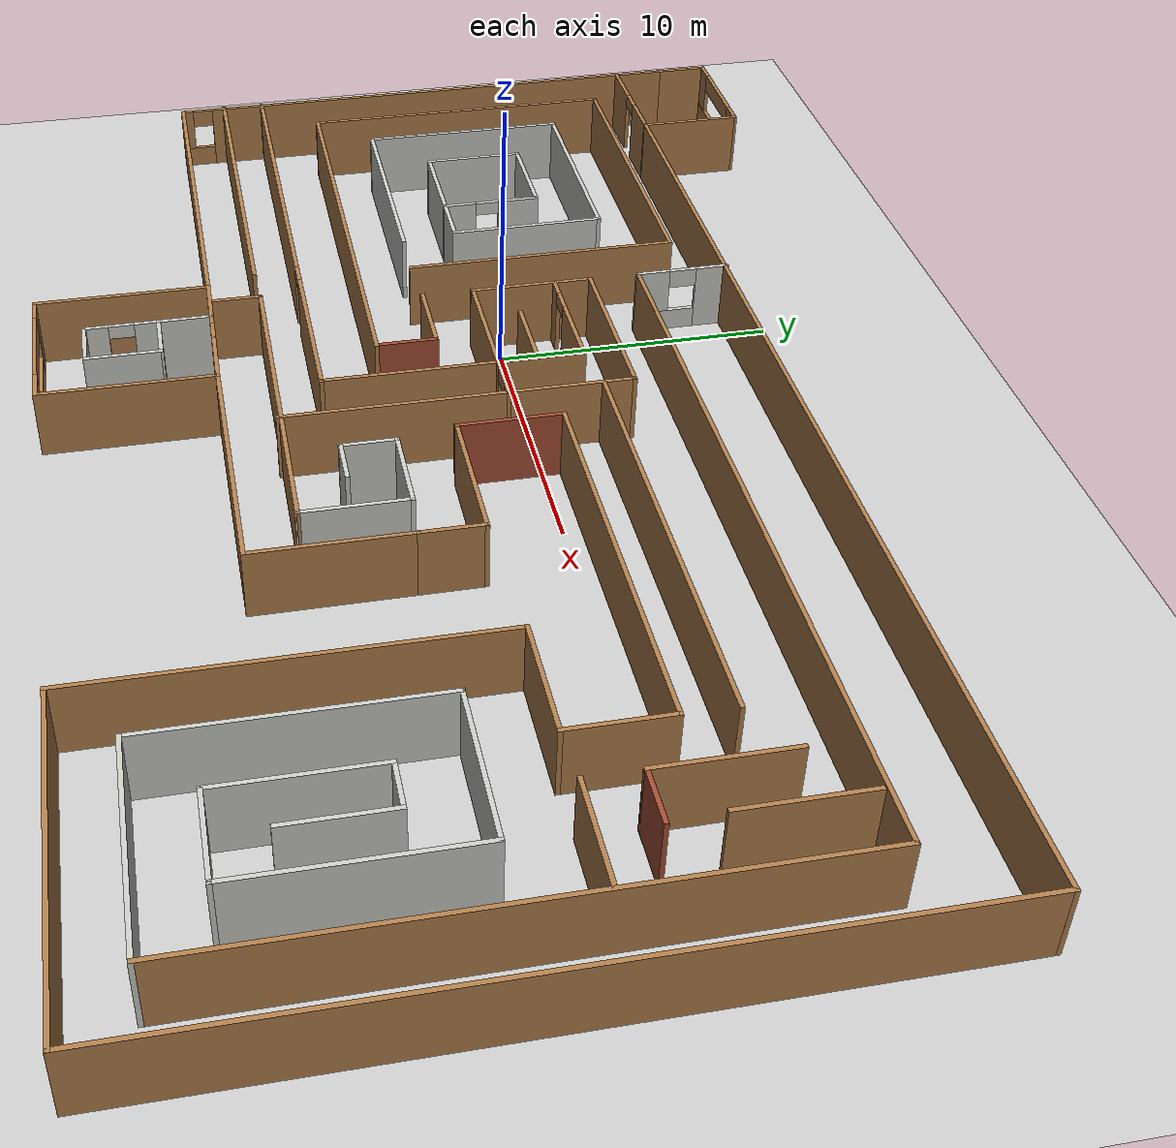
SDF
<sdf version="1.6">
 <world name="default">
  <plugin name="welcome" filename="libwelcome.so"/>
  <light name="sun" type="directional">
   <pose>0 0 10 0 -0 0</pose>
   <diffuse>0.8 0.8 0.8 1</diffuse>
   <specular>0.2 0.2 0.2 1</specular>
   <attenuation>
    <range>1000</range>
    <constant>0.9</constant>
    <linear>0.01</linear>
    <quadratic>0.001</quadratic>
   </attenuation>
   <direction>-0.5 0.1 -0.9</direction>
  </light>
  <model name="ground_plane">
   <static>1</static>
   <link name="link">
    <collision name="collision">
     <geometry><plane><normal>0 0 1</normal><size>100 100</size></plane></geometry>
     <surface><friction><ode><mu>100</mu><mu2>50</mu2></ode></friction></surface>
    </collision>
    <visual name="visual">
     <cast_shadows>0</cast_shadows>
     <geometry><plane><normal>0 0 1</normal><size>100 100</size></plane></geometry>
     <material>
      <script><uri>file://media/materials/scripts/gazebo.material</uri><name>Gazebo/Grey</name></script>
     </material>
    </visual>
   </link>
  </model>
  <gravity>0 0 -9.8</gravity>
  <magnetic_field>6e-06 2.3e-05 -4.2e-05</magnetic_field>
  <atmosphere type="adiabatic"/>
  <physics name="default_physics" default="0" type="ode">
   <max_step_size>0.001</max_step_size>
   <real_time_factor>1</real_time_factor>
   <real_time_update_rate>1000</real_time_update_rate>
  </physics>
  <scene><ambient>0.4 0.4 0.4 1</ambient><background>0.7 0.7 0.7 1</background><shadows>1</shadows></scene>
  <spherical_coordinates>
   <surface_model>EARTH_WGS84</surface_model>
   <latitude_deg>0</latitude_deg>
   <longitude_deg>0</longitude_deg>
   <elevation>0</elevation>
   <heading_deg>0</heading_deg>
  </spherical_coordinates>
  <model name="Building">
   <pose>5.7189 -2.01548 0 0 -0 0</pose>
   <link name="Wall_0">
    <pose>-22.4887 2.1266 0 0 0 -1.56733</pose>
    <visual name="Wall_0_Visual_0">
     <pose>-0.641349 0 1.25 0 -0 0</pose>
     <geometry><box><size>19.6144 0.15 2.5</size></box></geometry>
     <material>
      <script><uri>file://media/materials/scripts/gazebo.material</uri><name>Gazebo/Wood</name></script>
      <ambient>1 1 1 1</ambient>
     </material>
     <meta><layer>0</layer></meta>
    </visual>
    <collision name="Wall_0_Collision_0">
     <geometry><box><size>19.6144 0.15 2.5</size></box></geometry>
     <pose>-0.641349 0 1.25 0 -0 0</pose>
    </collision>
    <visual name="Wall_0_Visual_1">
     <pose>9.80721 0 0.4 0 -0 0</pose>
     <geometry><box><size>1.2827 0.15 0.8</size></box></geometry>
     <material>
      <script><uri>file://media/materials/scripts/gazebo.material</uri><name>Gazebo/Wood</name></script>
      <ambient>1 1 1 1</ambient>
     </material>
     <meta><layer>0</layer></meta>
    </visual>
    <collision name="Wall_0_Collision_1">
     <geometry><box><size>1.2827 0.15 0.8</size></box></geometry>
     <pose>9.80721 0 0.4 0 -0 0</pose>
    </collision>
    <visual name="Wall_0_Visual_2">
     <pose>10.2072 0 1.65 0 -0 0</pose>
     <geometry><box><size>0.482698 0.15 1.7</size></box></geometry>
     <material>
      <script><uri>file://media/materials/scripts/gazebo.material</uri><name>Gazebo/Wood</name></script>
      <ambient>1 1 1 1</ambient>
     </material>
     <meta><layer>0</layer></meta>
    </visual>
    <collision name="Wall_0_Collision_2">
     <geometry><box><size>0.482698 0.15 1.7</size></box></geometry>
     <pose>10.2072 0 1.65 0 -0 0</pose>
    </collision>
    <visual name="Wall_0_Visual_3">
     <pose>9.56587 0 2.15 0 -0 0</pose>
     <geometry><box><size>0.8 0.15 0.7</size></box></geometry>
     <material>
      <script><uri>file://media/materials/scripts/gazebo.material</uri><name>Gazebo/Wood</name></script>
      <ambient>1 1 1 1</ambient>
     </material>
     <meta><layer>0</layer></meta>
    </visual>
    <collision name="Wall_0_Collision_3">
     <geometry><box><size>0.8 0.15 0.7</size></box></geometry>
     <pose>9.56587 0 2.15 0 -0 0</pose>
    </collision>
   </link>
   <link name="Wall_1">
    <collision name="Wall_1_Collision">
     <geometry><box><size>13.928 0.15 2.5</size></box></geometry>
     <pose>0 0 1.25 0 -0 0</pose>
    </collision>
    <visual name="Wall_1_Visual">
     <pose>0 0 1.25 0 -0 0</pose>
     <geometry><box><size>13.928 0.15 2.5</size></box></geometry>
     <material>
      <script><uri>file://media/materials/scripts/gazebo.material</uri><name>Gazebo/Wood</name></script>
      <ambient>1 1 1 1</ambient>
     </material>
     <meta><layer>0</layer></meta>
    </visual>
    <pose>-15.5637 -8.2469 0 0 -0 0</pose>
   </link>
   <link name="Wall_10">
    <collision name="Wall_10_Collision">
     <geometry><box><size>14 0.15 2.5</size></box></geometry>
     <pose>0 0 1.25 0 -0 0</pose>
    </collision>
    <visual name="Wall_10_Visual">
     <pose>0 0 1.25 0 -0 0</pose>
     <geometry><box><size>14 0.15 2.5</size></box></geometry>
     <material>
      <script><uri>file://media/materials/scripts/gazebo.material</uri><name>Gazebo/Wood</name></script>
      <ambient>1 1 1 1</ambient>
     </material>
     <meta><layer>0</layer></meta>
    </visual>
    <pose>8.10018 2.69968 0 0 -0 0</pose>
   </link>
   <link name="Wall_11">
    <collision name="Wall_11_Collision">
     <geometry><box><size>3.5 0.15 2.5</size></box></geometry>
     <pose>0 0 1.25 0 -0 0</pose>
    </collision>
    <visual name="Wall_11_Visual">
     <pose>0 0 1.25 0 -0 0</pose>
     <geometry><box><size>3.5 0.15 2.5</size></box></geometry>
     <material>
      <script><uri>file://media/materials/scripts/gazebo.material</uri><name>Gazebo/Wood</name></script>
      <ambient>1 1 1 1</ambient>
     </material>
     <meta><layer>0</layer></meta>
    </visual>
    <pose>15.0252 1.02468 0 0 0 -1.5708</pose>
   </link>
   <link name="Wall_12">
    <collision name="Wall_12_Collision">
     <geometry><box><size>4.25 0.15 2.5</size></box></geometry>
     <pose>0 0 1.25 0 -0 0</pose>
    </collision>
    <visual name="Wall_12_Visual">
     <pose>0 0 1.25 0 -0 0</pose>
     <geometry><box><size>4.25 0.15 2.5</size></box></geometry>
     <material>
      <script><uri>file://media/materials/scripts/gazebo.material</uri><name>Gazebo/Wood</name></script>
      <ambient>1 1 1 1</ambient>
     </material>
     <meta><layer>0</layer></meta>
    </visual>
    <pose>12.9752 -0.650318 0 0 -0 3.14159</pose>
   </link>
   <link name="Wall_13">
    <collision name="Wall_13_Collision">
     <geometry><box><size>13.75 0.15 2.5</size></box></geometry>
     <pose>0 0 1.25 0 -0 0</pose>
    </collision>
    <visual name="Wall_13_Visual">
     <pose>0 0 1.25 0 -0 0</pose>
     <geometry><box><size>13.75 0.15 2.5</size></box></geometry>
     <material>
      <script><uri>file://media/materials/scripts/gazebo.material</uri><name>Gazebo/Wood</name></script>
      <ambient>1 1 1 1</ambient>
     </material>
     <meta><layer>0</layer></meta>
    </visual>
    <pose>10.9252 -7.45032 0 0 0 -1.5708</pose>
   </link>
   <link name="Wall_14">
    <collision name="Wall_14_Collision">
     <geometry><box><size>11.75 0.15 2.5</size></box></geometry>
     <pose>0 0 1.25 0 -0 0</pose>
    </collision>
    <visual name="Wall_14_Visual">
     <pose>0 0 1.25 0 -0 0</pose>
     <geometry><box><size>11.75 0.15 2.5</size></box></geometry>
     <material>
      <script><uri>file://media/materials/scripts/gazebo.material</uri><name>Gazebo/Wood</name></script>
      <ambient>1 1 1 1</ambient>
     </material>
     <meta><layer>0</layer></meta>
    </visual>
    <pose>16.7252 -14.2503 0 0 -0 0</pose>
   </link>
   <link name="Wall_15">
    <collision name="Wall_15_Collision">
     <geometry><box><size>25 0.15 2.5</size></box></geometry>
     <pose>0 0 1.25 0 -0 0</pose>
    </collision>
    <visual name="Wall_15_Visual">
     <pose>0 0 1.25 0 -0 0</pose>
     <geometry><box><size>25 0.15 2.5</size></box></geometry>
     <material>
      <script><uri>file://media/materials/scripts/gazebo.material</uri><name>Gazebo/Wood</name></script>
      <ambient>1 1 1 1</ambient>
     </material>
     <meta><layer>0</layer></meta>
    </visual>
    <pose>22.5252 -1.82532 0 0 -0 1.5708</pose>
   </link>
   <link name="Wall_16">
    <collision name="Wall_16_Collision">
     <geometry><box><size>40.5 0.15 2.5</size></box></geometry>
     <pose>0 0 1.25 0 -0 0</pose>
    </collision>
    <visual name="Wall_16_Visual">
     <pose>0 0 1.25 0 -0 0</pose>
     <geometry><box><size>40.5 0.15 2.5</size></box></geometry>
     <material>
      <script><uri>file://media/materials/scripts/gazebo.material</uri><name>Gazebo/Wood</name></script>
      <ambient>1 1 1 1</ambient>
     </material>
     <meta><layer>0</layer></meta>
    </visual>
    <pose>2.35024 10.5999 0 0 -0 3.14158</pose>
   </link>
   <link name="Wall_17">
    <collision name="Wall_17_Collision">
     <geometry><box><size>4 0.15 2.5</size></box></geometry>
     <pose>0 0 1.25 0 -0 0</pose>
    </collision>
    <visual name="Wall_17_Visual">
     <pose>0 0 1.25 0 -0 0</pose>
     <geometry><box><size>4 0.15 2.5</size></box></geometry>
     <material>
      <script><uri>file://media/materials/scripts/gazebo.material</uri><name>Gazebo/Wood</name></script>
      <ambient>1 1 1 1</ambient>
     </material>
     <meta><layer>0</layer></meta>
    </visual>
    <pose>-17.8248 12.5249 0 0 -0 1.57083</pose>
   </link>
   <link name="Wall_18">
    <pose>-20.1748 14.4499 0 0 -0 3.1415</pose>
    <visual name="Wall_18_Visual_0">
     <pose>-1.954 0 1.25 0 -0 0</pose>
     <geometry><box><size>0.941881 0.15 2.5</size></box></geometry>
     <material>
      <script><uri>file://media/materials/scripts/gazebo.material</uri><name>Gazebo/Wood</name></script>
      <ambient>1 1 1 1</ambient>
     </material>
     <meta><layer>0</layer></meta>
    </visual>
    <collision name="Wall_18_Collision_0">
     <geometry><box><size>0.941881 0.15 2.5</size></box></geometry>
     <pose>-1.954 0 1.25 0 -0 0</pose>
    </collision>
    <visual name="Wall_18_Visual_1">
     <pose>0.470941 0 0.4 0 -0 0</pose>
     <geometry><box><size>3.908 0.15 0.8</size></box></geometry>
     <material>
      <script><uri>file://media/materials/scripts/gazebo.material</uri><name>Gazebo/Wood</name></script>
      <ambient>1 1 1 1</ambient>
     </material>
     <meta><layer>0</layer></meta>
    </visual>
    <collision name="Wall_18_Collision_1">
     <geometry><box><size>3.908 0.15 0.8</size></box></geometry>
     <pose>0.470941 0 0.4 0 -0 0</pose>
    </collision>
    <visual name="Wall_18_Visual_2">
     <pose>1.97094 0 1.65 0 -0 0</pose>
     <geometry><box><size>0.907999 0.15 1.7</size></box></geometry>
     <material>
      <script><uri>file://media/materials/scripts/gazebo.material</uri><name>Gazebo/Wood</name></script>
      <ambient>1 1 1 1</ambient>
     </material>
     <meta><layer>0</layer></meta>
    </visual>
    <collision name="Wall_18_Collision_2">
     <geometry><box><size>0.907999 0.15 1.7</size></box></geometry>
     <pose>1.97094 0 1.65 0 -0 0</pose>
    </collision>
    <visual name="Wall_18_Visual_3">
     <pose>0.016941 0 2.15 0 -0 0</pose>
     <geometry><box><size>3 0.15 0.7</size></box></geometry>
     <material>
      <script><uri>file://media/materials/scripts/gazebo.material</uri><name>Gazebo/Wood</name></script>
      <ambient>1 1 1 1</ambient>
     </material>
     <meta><layer>0</layer></meta>
    </visual>
    <collision name="Wall_18_Collision_3">
     <geometry><box><size>3 0.15 0.7</size></box></geometry>
     <pose>0.016941 0 2.15 0 -0 0</pose>
    </collision>
   </link>
   <link name="Wall_19">
    <collision name="Wall_19_Collision">
     <geometry><box><size>2.1 0.15 2.5</size></box></geometry>
     <pose>0 0 1.25 0 -0 0</pose>
    </collision>
    <visual name="Wall_19_Visual">
     <pose>0 0 1.25 0 -0 0</pose>
     <geometry><box><size>2.1 0.15 2.5</size></box></geometry>
     <material>
      <script><uri>file://media/materials/scripts/gazebo.material</uri><name>Gazebo/Wood</name></script>
      <ambient>0.921569 0.807843 0.615686 1</ambient>
     </material>
     <meta><layer>0</layer></meta>
    </visual>
    <pose>-22.5247 13.4751 0 0 0 -1.5708</pose>
   </link>
   <link name="Wall_2">
    <collision name="Wall_2_Collision">
     <geometry><box><size>6.35342 0.15 2.5</size></box></geometry>
     <pose>0 0 1.25 0 -0 0</pose>
    </collision>
    <visual name="Wall_2_Visual">
     <pose>0 0 1.25 0 -0 0</pose>
     <geometry><box><size>6.35342 0.15 2.5</size></box></geometry>
     <material>
      <script><uri>file://media/materials/scripts/gazebo.material</uri><name>Gazebo/Wood</name></script>
      <ambient>1 1 1 1</ambient>
     </material>
     <meta><layer>0</layer></meta>
    </visual>
    <pose>-8.6747 -11.3484 0 0 0 -1.5708</pose>
   </link>
   <link name="Wall_22">
    <pose>-5.87476 -8.29861 0 0 -0 3.12313</pose>
    <visual name="Wall_22_Visual_0">
     <pose>-1.68319 0 1.25 0 -0 0</pose>
     <geometry><box><size>2.38444 0.15 2.5</size></box></geometry>
     <material>
      <script><uri>file://media/materials/scripts/gazebo.material</uri><name>Gazebo/Wood</name></script>
      <ambient>1 1 1 1</ambient>
     </material>
     <meta><layer>0</layer></meta>
    </visual>
    <collision name="Wall_22_Collision_0">
     <geometry><box><size>2.38444 0.15 2.5</size></box></geometry>
     <pose>-1.68319 0 1.25 0 -0 0</pose>
    </collision>
    <visual name="Wall_22_Visual_1">
     <pose>1.64222 0 1.25 0 -0 0</pose>
     <geometry><box><size>2.46639 0.15 2.5</size></box></geometry>
     <material>
      <script><uri>file://media/materials/scripts/gazebo.material</uri><name>Gazebo/Wood</name></script>
      <ambient>1 1 1 1</ambient>
     </material>
     <meta><layer>0</layer></meta>
    </visual>
    <collision name="Wall_22_Collision_1">
     <geometry><box><size>2.46639 0.15 2.5</size></box></geometry>
     <pose>1.64222 0 1.25 0 -0 0</pose>
    </collision>
    <visual name="Wall_22_Visual_2">
     <pose>-0.040973 0 2.25 0 -0 0</pose>
     <geometry><box><size>0.9 0.15 0.5</size></box></geometry>
     <material>
      <script><uri>file://media/materials/scripts/gazebo.material</uri><name>Gazebo/Wood</name></script>
      <ambient>1 1 1 1</ambient>
     </material>
     <meta><layer>0</layer></meta>
    </visual>
    <collision name="Wall_22_Collision_2">
     <geometry><box><size>0.9 0.15 0.5</size></box></geometry>
     <pose>-0.040973 0 2.25 0 -0 0</pose>
    </collision>
   </link>
   <link name="Wall_24">
    <collision name="Wall_24_Collision">
     <geometry><box><size>2 0.15 2.5</size></box></geometry>
     <pose>0 0 1.25 0 -0 0</pose>
    </collision>
    <visual name="Wall_24_Visual">
     <pose>0 0 1.25 0 -0 0</pose>
     <geometry><box><size>2 0.15 2.5</size></box></geometry>
     <material>
      <script><uri>file://media/materials/scripts/gazebo.material</uri><name>Gazebo/CeilingTiled</name></script>
      <ambient>1 1 1 1</ambient>
     </material>
     <meta><layer>0</layer></meta>
    </visual>
    <pose>-6.7275 -9.22377 0 0 0 -1.57101</pose>
   </link>
   <link name="Wall_25">
    <collision name="Wall_25_Collision">
     <geometry><box><size>2 0.15 2.5</size></box></geometry>
     <pose>0 0 1.25 0 -0 0</pose>
    </collision>
    <visual name="Wall_25_Visual">
     <pose>0 0 1.25 0 -0 0</pose>
     <geometry><box><size>2 0.15 2.5</size></box></geometry>
     <material>
      <script><uri>file://media/materials/scripts/gazebo.material</uri><name>Gazebo/CeilingTiled</name></script>
      <ambient>1 1 1 1</ambient>
     </material>
     <meta><layer>0</layer></meta>
    </visual>
    <pose>-5.8027 -10.1489 0 0 -0 0</pose>
   </link>
   <link name="Wall_27">
    <collision name="Wall_27_Collision">
     <geometry><box><size>2.75 0.15 2.5</size></box></geometry>
     <pose>0 0 1.25 0 -0 0</pose>
    </collision>
    <visual name="Wall_27_Visual">
     <pose>0 0 1.25 0 -0 0</pose>
     <geometry><box><size>2.75 0.15 2.5</size></box></geometry>
     <material>
      <script><uri>file://media/materials/scripts/gazebo.material</uri><name>Gazebo/CeilingTiled</name></script>
      <ambient>1 1 1 1</ambient>
     </material>
     <meta><layer>0</layer></meta>
    </visual>
    <pose>-4.8775 -11.4488 0 0 0 -1.57064</pose>
   </link>
   <link name="Wall_28">
    <collision name="Wall_28_Collision">
     <geometry><box><size>2.0004 0.15 2.5</size></box></geometry>
     <pose>0 0 1.25 0 -0 0</pose>
    </collision>
    <visual name="Wall_28_Visual">
     <pose>0 0 1.25 0 -0 0</pose>
     <geometry><box><size>2.0004 0.15 2.5</size></box></geometry>
     <material>
      <script><uri>file://media/materials/scripts/gazebo.material</uri><name>Gazebo/CeilingTiled</name></script>
      <ambient>1 1 1 1</ambient>
     </material>
     <meta><layer>0</layer></meta>
    </visual>
    <pose>-5.8025 -12.7488 0 0 0 -3.14146</pose>
   </link>
   <link name="Wall_29">
    <pose>-6.7277 -11.4489 0 0 -0 1.5708</pose>
    <visual name="Wall_29_Visual_0">
     <pose>-0.915206 0 1.25 0 -0 0</pose>
     <geometry><box><size>0.919835 0.15 2.5</size></box></geometry>
     <material>
      <script><uri>file://media/materials/scripts/gazebo.material</uri><name>Gazebo/CeilingTiled</name></script>
      <ambient>1 1 1 1</ambient>
     </material>
     <meta><layer>0</layer></meta>
    </visual>
    <collision name="Wall_29_Collision_0">
     <geometry><box><size>0.919835 0.15 2.5</size></box></geometry>
     <pose>-0.915206 0 1.25 0 -0 0</pose>
    </collision>
    <visual name="Wall_29_Visual_1">
     <pose>0.909917 0 1.25 0 -0 0</pose>
     <geometry><box><size>0.930411 0.15 2.5</size></box></geometry>
     <material>
      <script><uri>file://media/materials/scripts/gazebo.material</uri><name>Gazebo/CeilingTiled</name></script>
      <ambient>1 1 1 1</ambient>
     </material>
     <meta><layer>0</layer></meta>
    </visual>
    <collision name="Wall_29_Collision_1">
     <geometry><box><size>0.930411 0.15 2.5</size></box></geometry>
     <pose>0.909917 0 1.25 0 -0 0</pose>
    </collision>
    <visual name="Wall_29_Visual_2">
     <pose>-0.005288 0 2.25 0 -0 0</pose>
     <geometry><box><size>0.9 0.15 0.5</size></box></geometry>
     <material>
      <script><uri>file://media/materials/scripts/gazebo.material</uri><name>Gazebo/CeilingTiled</name></script>
      <ambient>1 1 1 1</ambient>
     </material>
     <meta><layer>0</layer></meta>
    </visual>
    <collision name="Wall_29_Collision_2">
     <geometry><box><size>0.9 0.15 0.5</size></box></geometry>
     <pose>-0.005288 0 2.25 0 -0 0</pose>
    </collision>
   </link>
   <link name="Wall_3">
    <pose>-5.8747 -14.4499 0 0 -0 0</pose>
    <visual name="Wall_3_Visual_0">
     <pose>-2.37464 0 1.25 0 -0 0</pose>
     <geometry><box><size>1.00072 0.15 2.5</size></box></geometry>
     <material>
      <script><uri>file://media/materials/scripts/gazebo.material</uri><name>Gazebo/Wood</name></script>
      <ambient>1 1 1 1</ambient>
     </material>
     <meta><layer>0</layer></meta>
    </visual>
    <collision name="Wall_3_Collision_0">
     <geometry><box><size>1.00072 0.15 2.5</size></box></geometry>
     <pose>-2.37464 0 1.25 0 -0 0</pose>
    </collision>
    <visual name="Wall_3_Visual_1">
     <pose>0.50036 0 0.4 0 -0 0</pose>
     <geometry><box><size>4.74928 0.15 0.8</size></box></geometry>
     <material>
      <script><uri>file://media/materials/scripts/gazebo.material</uri><name>Gazebo/Wood</name></script>
      <ambient>1 1 1 1</ambient>
     </material>
     <meta><layer>0</layer></meta>
    </visual>
    <collision name="Wall_3_Collision_1">
     <geometry><box><size>4.74928 0.15 0.8</size></box></geometry>
     <pose>0.50036 0 0.4 0 -0 0</pose>
    </collision>
    <visual name="Wall_3_Visual_2">
     <pose>2.25036 0 1.65 0 -0 0</pose>
     <geometry><box><size>1.24928 0.15 1.7</size></box></geometry>
     <material>
      <script><uri>file://media/materials/scripts/gazebo.material</uri><name>Gazebo/Wood</name></script>
      <ambient>1 1 1 1</ambient>
     </material>
     <meta><layer>0</layer></meta>
    </visual>
    <collision name="Wall_3_Collision_2">
     <geometry><box><size>1.24928 0.15 1.7</size></box></geometry>
     <pose>2.25036 0 1.65 0 -0 0</pose>
    </collision>
    <visual name="Wall_3_Visual_3">
     <pose>-0.124281 0 2.15 0 -0 0</pose>
     <geometry><box><size>3.5 0.15 0.7</size></box></geometry>
     <material>
      <script><uri>file://media/materials/scripts/gazebo.material</uri><name>Gazebo/Wood</name></script>
      <ambient>1 1 1 1</ambient>
     </material>
     <meta><layer>0</layer></meta>
    </visual>
    <collision name="Wall_3_Collision_3">
     <geometry><box><size>3.5 0.15 0.7</size></box></geometry>
     <pose>-0.124281 0 2.15 0 -0 0</pose>
    </collision>
   </link>
   <link name="Wall_31">
    <collision name="Wall_31_Collision">
     <geometry><box><size>1.94917 0.15 2.5</size></box></geometry>
     <pose>0 0 1.25 0 -0 0</pose>
    </collision>
    <visual name="Wall_31_Visual">
     <pose>0 0 1.25 0 -0 0</pose>
     <geometry><box><size>1.94917 0.15 2.5</size></box></geometry>
     <material>
      <script><uri>file://media/materials/scripts/gazebo.material</uri><name>Gazebo/Wood</name></script>
      <ambient>1 1 1 1</ambient>
     </material>
     <meta><layer>0</layer></meta>
    </visual>
    <pose>-7.6987 -7.3474 0 0 -0 1.5708</pose>
   </link>
   <link name="Wall_32">
    <collision name="Wall_32_Collision">
     <geometry><box><size>12.5011 0.15 2.5</size></box></geometry>
     <pose>0 0 1.25 0 -0 0</pose>
    </collision>
    <visual name="Wall_32_Visual">
     <pose>0 0 1.25 0 -0 0</pose>
     <geometry><box><size>12.5011 0.15 2.5</size></box></geometry>
     <material>
      <script><uri>file://media/materials/scripts/gazebo.material</uri><name>Gazebo/Wood</name></script>
      <ambient>1 1 1 1</ambient>
     </material>
     <meta><layer>0</layer></meta>
    </visual>
    <pose>-1.52347 -6.48873 0 0 0 -0.006612</pose>
   </link>
   <link name="Wall_33">
    <collision name="Wall_33_Collision">
     <geometry><box><size>3.75 0.15 2.5</size></box></geometry>
     <pose>0 0 1.25 0 -0 0</pose>
    </collision>
    <visual name="Wall_33_Visual">
     <pose>0 0 1.25 0 -0 0</pose>
     <geometry><box><size>3.75 0.15 2.5</size></box></geometry>
     <material>
      <script><uri>file://media/materials/scripts/gazebo.material</uri><name>Gazebo/CeilingTiled</name></script>
      <ambient>1 1 1 1</ambient>
     </material>
     <meta><layer>0</layer></meta>
    </visual>
    <pose>4.65177 -4.72956 0 0 -0 1.5708</pose>
   </link>
   <link name="Wall_34">
    <collision name="Wall_34_Collision">
     <geometry><box><size>3.25 0.15 2.5</size></box></geometry>
     <pose>0 0 1.25 0 -0 0</pose>
    </collision>
    <visual name="Wall_34_Visual">
     <pose>0 0 1.25 0 -0 0</pose>
     <geometry><box><size>3.25 0.15 2.5</size></box></geometry>
     <material>
      <script><uri>file://media/materials/scripts/gazebo.material</uri><name>Gazebo/CeilingTiled</name></script>
      <ambient>1 1 1 1</ambient>
     </material>
     <meta><layer>0</layer></meta>
    </visual>
    <pose>3.10177 -2.92956 0 0 -0 3.14159</pose>
   </link>
   <link name="Wall_35">
    <collision name="Wall_35_Collision">
     <geometry><box><size>2 0.15 2.5</size></box></geometry>
     <pose>0 0 1.25 0 -0 0</pose>
    </collision>
    <visual name="Wall_35_Visual">
     <pose>0 0 1.25 0 -0 0</pose>
     <geometry><box><size>2 0.15 2.5</size></box></geometry>
     <material>
      <script><uri>file://media/materials/scripts/gazebo.material</uri><name>Gazebo/CeilingTiled</name></script>
      <ambient>1 1 1 1</ambient>
     </material>
     <meta><layer>0</layer></meta>
    </visual>
    <pose>1.55177 -3.85456 0 0 0 -1.5708</pose>
   </link>
   <link name="Wall_36">
    <collision name="Wall_36_Collision">
     <geometry><box><size>1.75 0.15 2.5</size></box></geometry>
     <pose>0 0 1.25 0 -0 0</pose>
    </collision>
    <visual name="Wall_36_Visual">
     <pose>0 0 1.25 0 -0 0</pose>
     <geometry><box><size>1.75 0.15 2.5</size></box></geometry>
     <material>
      <script><uri>file://media/materials/scripts/gazebo.material</uri><name>Gazebo/CeilingTiled</name></script>
      <ambient>1 1 1 1</ambient>
     </material>
     <meta><layer>0</layer></meta>
    </visual>
    <pose>2.35177 -4.77956 0 0 -0 0</pose>
   </link>
   <link name="Wall_38">
    <collision name="Wall_38_Collision">
     <geometry><box><size>12.25 0.15 2.5</size></box></geometry>
     <pose>0 0 1.25 0 -0 0</pose>
    </collision>
    <visual name="Wall_38_Visual">
     <pose>0 0 1.25 0 -0 0</pose>
     <geometry><box><size>12.25 0.15 2.5</size></box></geometry>
     <material>
      <script><uri>file://media/materials/scripts/gazebo.material</uri><name>Gazebo/Wood</name></script>
      <ambient>1 1 1 1</ambient>
     </material>
     <meta><layer>0</layer></meta>
    </visual>
    <pose>-0.3357 -0.549898 0 0 -0 1.5708</pose>
   </link>
   <link name="Wall_39">
    <collision name="Wall_39_Collision">
     <geometry><box><size>6.5 0.15 2.5</size></box></geometry>
     <pose>0 0 1.25 0 -0 0</pose>
    </collision>
    <visual name="Wall_39_Visual">
     <pose>0 0 1.25 0 -0 0</pose>
     <geometry><box><size>6.5 0.15 2.5</size></box></geometry>
     <material>
      <script><uri>file://media/materials/scripts/gazebo.material</uri><name>Gazebo/Wood</name></script>
      <ambient>1 1 1 1</ambient>
     </material>
     <meta><layer>0</layer></meta>
    </visual>
    <pose>-3.51051 5.50029 0 0 -0 3.14153</pose>
   </link>
   <link name="Wall_4">
    <collision name="Wall_4_Collision">
     <geometry><box><size>6.25 0.15 2.5</size></box></geometry>
     <pose>0 0 1.25 0 -0 0</pose>
    </collision>
    <visual name="Wall_4_Visual">
     <pose>0 0 1.25 0 -0 0</pose>
     <geometry><box><size>6.25 0.15 2.5</size></box></geometry>
     <material>
      <script><uri>file://media/materials/scripts/gazebo.material</uri><name>Gazebo/Wood</name></script>
      <ambient>1 1 1 1</ambient>
     </material>
     <meta><layer>0</layer></meta>
    </visual>
    <pose>-3.07476 -11.4001 0 0 -0 1.57082</pose>
   </link>
   <link name="Wall_40">
    <collision name="Wall_40_Collision">
     <geometry><box><size>4.5 0.15 2.5</size></box></geometry>
     <pose>0 0 1.25 0 -0 0</pose>
    </collision>
    <visual name="Wall_40_Visual">
     <pose>0 0 1.25 0 -0 0</pose>
     <geometry><box><size>4.5 0.15 2.5</size></box></geometry>
     <material>
      <script><uri>file://media/materials/scripts/gazebo.material</uri><name>Gazebo/Wood</name></script>
      <ambient>1 1 1 1</ambient>
     </material>
     <meta><layer>0</layer></meta>
    </visual>
    <pose>-6.68532 3.32548 0 0 0 -1.5708</pose>
   </link>
   <link name="Wall_41">
    <pose>-3.51032 1.15048 0 0 -0 0</pose>
    <visual name="Wall_41_Visual_0">
     <pose>-0.707511 0 1.25 0 -0 0</pose>
     <geometry><box><size>5.08498 0.15 2.5</size></box></geometry>
     <material>
      <script><uri>file://media/materials/scripts/gazebo.material</uri><name>Gazebo/Wood</name></script>
      <ambient>1 1 1 1</ambient>
     </material>
     <meta><layer>0</layer></meta>
    </visual>
    <collision name="Wall_41_Collision_0">
     <geometry><box><size>5.08498 0.15 2.5</size></box></geometry>
     <pose>-0.707511 0 1.25 0 -0 0</pose>
    </collision>
    <visual name="Wall_41_Visual_1">
     <pose>2.99249 0 1.25 0 -0 0</pose>
     <geometry><box><size>0.515021 0.15 2.5</size></box></geometry>
     <material>
      <script><uri>file://media/materials/scripts/gazebo.material</uri><name>Gazebo/Wood</name></script>
      <ambient>1 1 1 1</ambient>
     </material>
     <meta><layer>0</layer></meta>
    </visual>
    <collision name="Wall_41_Collision_1">
     <geometry><box><size>0.515021 0.15 2.5</size></box></geometry>
     <pose>2.99249 0 1.25 0 -0 0</pose>
    </collision>
    <visual name="Wall_41_Visual_2">
     <pose>2.28498 0 2.25 0 -0 0</pose>
     <geometry><box><size>0.9 0.15 0.5</size></box></geometry>
     <material>
      <script><uri>file://media/materials/scripts/gazebo.material</uri><name>Gazebo/Wood</name></script>
      <ambient>1 1 1 1</ambient>
     </material>
     <meta><layer>0</layer></meta>
    </visual>
    <collision name="Wall_41_Collision_2">
     <geometry><box><size>0.9 0.15 0.5</size></box></geometry>
     <pose>2.28498 0 2.25 0 -0 0</pose>
    </collision>
   </link>
   <link name="Wall_43">
    <collision name="Wall_43_Collision">
     <geometry><box><size>9.25 0.15 2.5</size></box></geometry>
     <pose>0 0 1.25 0 -0 0</pose>
    </collision>
    <visual name="Wall_43_Visual">
     <pose>0 0 1.25 0 -0 0</pose>
     <geometry><box><size>9.25 0.15 2.5</size></box></geometry>
     <material>
      <script><uri>file://media/materials/scripts/gazebo.material</uri><name>Gazebo/Wood</name></script>
      <ambient>1 1 1 1</ambient>
     </material>
     <meta><layer>0</layer></meta>
    </visual>
    <pose>-2.1157 -0.387898 0 0 0 -1.5708</pose>
   </link>
   <link name="Wall_44">
    <pose>-12.3202 -4.9379 0 0 -0 3.14159</pose>
    <visual name="Wall_44_Visual_0">
     <pose>-7.02658 0 1.25 0 -0 0</pose>
     <geometry><box><size>6.50584 0.15 2.5</size></box></geometry>
     <material>
      <script><uri>file://media/materials/scripts/gazebo.material</uri><name>Gazebo/Wood</name></script>
      <ambient>1 1 1 1</ambient>
     </material>
     <meta><layer>0</layer></meta>
    </visual>
    <collision name="Wall_44_Collision_0">
     <geometry><box><size>6.50584 0.15 2.5</size></box></geometry>
     <pose>-7.02658 0 1.25 0 -0 0</pose>
    </collision>
    <visual name="Wall_44_Visual_1">
     <pose>3.70292 0 1.25 0 -0 0</pose>
     <geometry><box><size>13.1532 0.15 2.5</size></box></geometry>
     <material>
      <script><uri>file://media/materials/scripts/gazebo.material</uri><name>Gazebo/Wood</name></script>
      <ambient>1 1 1 1</ambient>
     </material>
     <meta><layer>0</layer></meta>
    </visual>
    <collision name="Wall_44_Collision_1">
     <geometry><box><size>13.1532 0.15 2.5</size></box></geometry>
     <pose>3.70292 0 1.25 0 -0 0</pose>
    </collision>
    <visual name="Wall_44_Visual_2">
     <pose>-3.32366 0 2.25 0 -0 0</pose>
     <geometry><box><size>0.9 0.15 0.5</size></box></geometry>
     <material>
      <script><uri>file://media/materials/scripts/gazebo.material</uri><name>Gazebo/Wood</name></script>
      <ambient>1 1 1 1</ambient>
     </material>
     <meta><layer>0</layer></meta>
    </visual>
    <collision name="Wall_44_Collision_2">
     <geometry><box><size>0.9 0.15 0.5</size></box></geometry>
     <pose>-3.32366 0 2.25 0 -0 0</pose>
    </collision>
   </link>
   <link name="Wall_45">
    <collision name="Wall_45_Collision">
     <geometry><box><size>0.359336 0.15 2.5</size></box></geometry>
     <pose>0 0 1.25 0 -0 0</pose>
    </collision>
    <visual name="Wall_45_Visual">
     <pose>0 0 1.25 0 -0 0</pose>
     <geometry><box><size>0.359336 0.15 2.5</size></box></geometry>
     <material>
      <script><uri>file://media/materials/scripts/gazebo.material</uri><name>Gazebo/Grey</name></script>
      <ambient>1 1 1 1</ambient>
     </material>
     <meta><layer>0</layer></meta>
    </visual>
    <pose>-22.42 -4.93812 0 0 0 -0.002083</pose>
   </link>
   <link name="Wall_47">
    <collision name="Wall_47_Collision">
     <geometry><box><size>3 0.15 2.5</size></box></geometry>
     <pose>0 0 1.25 0 -0 0</pose>
    </collision>
    <visual name="Wall_47_Visual">
     <pose>0 0 1.25 0 -0 0</pose>
     <geometry><box><size>3 0.15 2.5</size></box></geometry>
     <material>
      <script><uri>file://media/materials/scripts/gazebo.material</uri><name>Gazebo/Wood</name></script>
      <ambient>1 1 1 1</ambient>
     </material>
     <meta><layer>0</layer></meta>
    </visual>
    <pose>-3.60317 2.54344 0 0 -0 0</pose>
   </link>
   <link name="Wall_5">
    <collision name="Wall_5_Collision">
     <geometry><box><size>9.5 0.15 2.5</size></box></geometry>
     <pose>0 0 1.25 0 -0 0</pose>
    </collision>
    <visual name="Wall_5_Visual">
     <pose>0 0 1.25 0 -0 0</pose>
     <geometry><box><size>9.5 0.15 2.5</size></box></geometry>
     <material>
      <script><uri>file://media/materials/scripts/gazebo.material</uri><name>Gazebo/Wood</name></script>
      <ambient>1 1 1 1</ambient>
     </material>
     <meta><layer>0</layer></meta>
    </visual>
    <pose>1.60018 -8.35032 0 0 -0 0</pose>
   </link>
   <link name="Wall_50">
    <pose>-4.4007 4.1621 0 0 -0 3.14159</pose>
    <visual name="Wall_50_Visual_0">
     <pose>-0.848534 0 1.25 0 -0 0</pose>
     <geometry><box><size>3.02293 0.15 2.5</size></box></geometry>
     <material>
      <script><uri>file://media/materials/scripts/gazebo.material</uri><name>Gazebo/Wood</name></script>
      <ambient>1 1 1 1</ambient>
     </material>
     <meta><layer>0</layer></meta>
    </visual>
    <collision name="Wall_50_Collision_0">
     <geometry><box><size>3.02293 0.15 2.5</size></box></geometry>
     <pose>-0.848534 0 1.25 0 -0 0</pose>
    </collision>
    <visual name="Wall_50_Visual_1">
     <pose>1.96147 0 1.25 0 -0 0</pose>
     <geometry><box><size>0.797068 0.15 2.5</size></box></geometry>
     <material>
      <script><uri>file://media/materials/scripts/gazebo.material</uri><name>Gazebo/Wood</name></script>
      <ambient>1 1 1 1</ambient>
     </material>
     <meta><layer>0</layer></meta>
    </visual>
    <collision name="Wall_50_Collision_1">
     <geometry><box><size>0.797068 0.15 2.5</size></box></geometry>
     <pose>1.96147 0 1.25 0 -0 0</pose>
    </collision>
    <visual name="Wall_50_Visual_2">
     <pose>1.11293 0 2.25 0 -0 0</pose>
     <geometry><box><size>0.9 0.15 0.5</size></box></geometry>
     <material>
      <script><uri>file://media/materials/scripts/gazebo.material</uri><name>Gazebo/Wood</name></script>
      <ambient>1 1 1 1</ambient>
     </material>
     <meta><layer>0</layer></meta>
    </visual>
    <collision name="Wall_50_Collision_2">
     <geometry><box><size>0.9 0.15 0.5</size></box></geometry>
     <pose>1.11293 0 2.25 0 -0 0</pose>
    </collision>
   </link>
   <link name="Wall_52">
    <collision name="Wall_52_Collision">
     <geometry><box><size>13.439 0.15 2.5</size></box></geometry>
     <pose>0 0 1.25 0 -0 0</pose>
    </collision>
    <visual name="Wall_52_Visual">
     <pose>0 0 1.25 0 -0 0</pose>
     <geometry><box><size>13.439 0.15 2.5</size></box></geometry>
     <material>
      <script><uri>file://media/materials/scripts/gazebo.material</uri><name>Gazebo/Wood</name></script>
      <ambient>1 1 1 1</ambient>
     </material>
     <meta><layer>0</layer></meta>
    </visual>
    <pose>-15.8802 -6.5189 0 0 -0 3.14159</pose>
   </link>
   <link name="Wall_54">
    <collision name="Wall_54_Collision">
     <geometry><box><size>3 0.15 2.5</size></box></geometry>
     <pose>0 0 1.25 0 -0 0</pose>
    </collision>
    <visual name="Wall_54_Visual">
     <pose>0 0 1.25 0 -0 0</pose>
     <geometry><box><size>3 0.15 2.5</size></box></geometry>
     <material>
      <script><uri>file://media/materials/scripts/gazebo.material</uri><name>Gazebo/Wood</name></script>
      <ambient>1 1 1 1</ambient>
     </material>
     <meta><layer>0</layer></meta>
    </visual>
    <pose>-5.3023 -0.693004 0 0 -0 0</pose>
   </link>
   <link name="Wall_55">
    <collision name="Wall_55_Collision">
     <geometry><box><size>2.25 0.15 2.5</size></box></geometry>
     <pose>0 0 1.25 0 -0 0</pose>
    </collision>
    <visual name="Wall_55_Visual">
     <pose>0 0 1.25 0 -0 0</pose>
     <geometry><box><size>2.25 0.15 2.5</size></box></geometry>
     <material>
      <script><uri>file://media/materials/scripts/gazebo.material</uri><name>Gazebo/Bricks</name></script>
      <ambient>1 1 1 1</ambient>
     </material>
     <meta><layer>0</layer></meta>
    </visual>
    <pose>-3.8773 -1.743 0 0 0 -1.5708</pose>
   </link>
   <link name="Wall_56">
    <collision name="Wall_56_Collision">
     <geometry><box><size>16.75 0.15 2.5</size></box></geometry>
     <pose>0 0 1.25 0 -0 0</pose>
    </collision>
    <visual name="Wall_56_Visual">
     <pose>0 0 1.25 0 -0 0</pose>
     <geometry><box><size>16.75 0.15 2.5</size></box></geometry>
     <material>
      <script><uri>file://media/materials/scripts/gazebo.material</uri><name>Gazebo/Wood</name></script>
      <ambient>1 1 1 1</ambient>
     </material>
     <meta><layer>0</layer></meta>
    </visual>
    <pose>-12.1773 -2.793 0 0 -0 3.14159</pose>
   </link>
   <link name="Wall_57">
    <collision name="Wall_57_Collision">
     <geometry><box><size>12 0.15 2.5</size></box></geometry>
     <pose>0 0 1.25 0 -0 0</pose>
    </collision>
    <visual name="Wall_57_Visual">
     <pose>0 0 1.25 0 -0 0</pose>
     <geometry><box><size>12 0.15 2.5</size></box></geometry>
     <material>
      <script><uri>file://media/materials/scripts/gazebo.material</uri><name>Gazebo/Wood</name></script>
      <ambient>1 1 1 1</ambient>
     </material>
     <meta><layer>0</layer></meta>
    </visual>
    <pose>-20.4773 3.132 0 0 -0 1.5708</pose>
   </link>
   <link name="Wall_58">
    <collision name="Wall_58_Collision">
     <geometry><box><size>12 0.15 2.5</size></box></geometry>
     <pose>0 0 1.25 0 -0 0</pose>
    </collision>
    <visual name="Wall_58_Visual">
     <pose>0 0 1.25 0 -0 0</pose>
     <geometry><box><size>12 0.15 2.5</size></box></geometry>
     <material>
      <script><uri>file://media/materials/scripts/gazebo.material</uri><name>Gazebo/Wood</name></script>
      <ambient>1 1 1 1</ambient>
     </material>
     <meta><layer>0</layer></meta>
    </visual>
    <pose>-14.5523 9.057 0 0 -0 0</pose>
   </link>
   <link name="Wall_59">
    <collision name="Wall_59_Collision">
     <geometry><box><size>10 0.15 2.5</size></box></geometry>
     <pose>0 0 1.25 0 -0 0</pose>
    </collision>
    <visual name="Wall_59_Visual">
     <pose>0 0 1.25 0 -0 0</pose>
     <geometry><box><size>10 0.15 2.5</size></box></geometry>
     <material>
      <script><uri>file://media/materials/scripts/gazebo.material</uri><name>Gazebo/Wood</name></script>
      <ambient>1 1 1 1</ambient>
     </material>
     <meta><layer>0</layer></meta>
    </visual>
    <pose>-8.6273 4.132 0 0 0 -1.5708</pose>
   </link>
   <link name="Wall_6">
    <collision name="Wall_6_Collision">
     <geometry><box><size>5.5 0.15 2.5</size></box></geometry>
     <pose>0 0 1.25 0 -0 0</pose>
    </collision>
    <visual name="Wall_6_Visual">
     <pose>0 0 1.25 0 -0 0</pose>
     <geometry><box><size>5.5 0.15 2.5</size></box></geometry>
     <material>
      <script><uri>file://media/materials/scripts/gazebo.material</uri><name>Gazebo/Wood</name></script>
      <ambient>1 1 1 1</ambient>
     </material>
     <meta><layer>0</layer></meta>
    </visual>
    <pose>6.27518 -5.67532 0 0 -0 1.5708</pose>
   </link>
   <link name="Wall_61">
    <collision name="Wall_61_Collision">
     <geometry><box><size>8.25 0.15 2.5</size></box></geometry>
     <pose>0 0 1.25 0 -0 0</pose>
    </collision>
    <visual name="Wall_61_Visual">
     <pose>0 0 1.25 0 -0 0</pose>
     <geometry><box><size>8.25 0.15 2.5</size></box></geometry>
     <material>
      <script><uri>file://media/materials/scripts/gazebo.material</uri><name>Gazebo/CeilingTiled</name></script>
      <ambient>1 1 1 1</ambient>
     </material>
     <meta><layer>0</layer></meta>
    </visual>
    <pose>-14.5801 -0.773915 0 0 -0 3.14159</pose>
   </link>
   <link name="Wall_62">
    <collision name="Wall_62_Collision">
     <geometry><box><size>7.75 0.15 2.5</size></box></geometry>
     <pose>0 0 1.25 0 -0 0</pose>
    </collision>
    <visual name="Wall_62_Visual">
     <pose>0 0 1.25 0 -0 0</pose>
     <geometry><box><size>7.75 0.15 2.5</size></box></geometry>
     <material>
      <script><uri>file://media/materials/scripts/gazebo.material</uri><name>Gazebo/CeilingTiled</name></script>
      <ambient>1 1 1 1</ambient>
     </material>
     <meta><layer>0</layer></meta>
    </visual>
    <pose>-18.6301 3.02609 0 0 -0 1.5708</pose>
   </link>
   <link name="Wall_63">
    <collision name="Wall_63_Collision">
     <geometry><box><size>8 0.15 2.5</size></box></geometry>
     <pose>0 0 1.25 0 -0 0</pose>
    </collision>
    <visual name="Wall_63_Visual">
     <pose>0 0 1.25 0 -0 0</pose>
     <geometry><box><size>8 0.15 2.5</size></box></geometry>
     <material>
      <script><uri>file://media/materials/scripts/gazebo.material</uri><name>Gazebo/CeilingTiled</name></script>
      <ambient>1 1 1 1</ambient>
     </material>
     <meta><layer>0</layer></meta>
    </visual>
    <pose>-14.7051 6.82609 0 0 -0 0</pose>
   </link>
   <link name="Wall_64">
    <collision name="Wall_64_Collision">
     <geometry><box><size>5.75 0.15 2.5</size></box></geometry>
     <pose>0 0 1.25 0 -0 0</pose>
    </collision>
    <visual name="Wall_64_Visual">
     <pose>0 0 1.25 0 -0 0</pose>
     <geometry><box><size>5.75 0.15 2.5</size></box></geometry>
     <material>
      <script><uri>file://media/materials/scripts/gazebo.material</uri><name>Gazebo/CeilingTiled</name></script>
      <ambient>1 1 1 1</ambient>
     </material>
     <meta><layer>0</layer></meta>
    </visual>
    <pose>-10.7799 4.02609 0 0 0 -1.57072</pose>
   </link>
   <link name="Wall_65">
    <collision name="Wall_65_Collision">
     <geometry><box><size>5.75 0.15 2.5</size></box></geometry>
     <pose>0 0 1.25 0 -0 0</pose>
    </collision>
    <visual name="Wall_65_Visual">
     <pose>0 0 1.25 0 -0 0</pose>
     <geometry><box><size>5.75 0.15 2.5</size></box></geometry>
     <material>
      <script><uri>file://media/materials/scripts/gazebo.material</uri><name>Gazebo/CeilingTiled</name></script>
      <ambient>1 1 1 1</ambient>
     </material>
     <meta><layer>0</layer></meta>
    </visual>
    <pose>-13.5797 1.2261 0 0 -0 3.14159</pose>
   </link>
   <link name="Wall_66">
    <collision name="Wall_66_Collision">
     <geometry><box><size>3.75 0.15 2.5</size></box></geometry>
     <pose>0 0 1.25 0 -0 0</pose>
    </collision>
    <visual name="Wall_66_Visual">
     <pose>0 0 1.25 0 -0 0</pose>
     <geometry><box><size>3.75 0.15 2.5</size></box></geometry>
     <material>
      <script><uri>file://media/materials/scripts/gazebo.material</uri><name>Gazebo/CeilingTiled</name></script>
      <ambient>0.435294 0.796078 0.67451 1</ambient>
     </material>
     <meta><layer>0</layer></meta>
    </visual>
    <pose>-16.3799 3.02609 0 0 -0 1.57091</pose>
   </link>
   <link name="Wall_67">
    <collision name="Wall_67_Collision">
     <geometry><box><size>3.75 0.15 2.5</size></box></geometry>
     <pose>0 0 1.25 0 -0 0</pose>
    </collision>
    <visual name="Wall_67_Visual">
     <pose>0 0 1.25 0 -0 0</pose>
     <geometry><box><size>3.75 0.15 2.5</size></box></geometry>
     <material>
      <script><uri>file://media/materials/scripts/gazebo.material</uri><name>Gazebo/CeilingTiled</name></script>
      <ambient>1 1 1 1</ambient>
     </material>
     <meta><layer>0</layer></meta>
    </visual>
    <pose>-14.5799 4.82609 0 0 -0 5e-06</pose>
   </link>
   <link name="Wall_68">
    <pose>-12.7797 3.0261 0 0 0 -1.5708</pose>
    <visual name="Wall_68_Visual_0">
     <pose>-1.08299 0 1.25 0 -0 0</pose>
     <geometry><box><size>1.58401 0.15 2.5</size></box></geometry>
     <material>
      <script><uri>file://media/materials/scripts/gazebo.material</uri><name>Gazebo/CeilingTiled</name></script>
      <ambient>1 1 1 1</ambient>
     </material>
     <meta><layer>0</layer></meta>
    </visual>
    <collision name="Wall_68_Collision_0">
     <geometry><box><size>1.58401 0.15 2.5</size></box></geometry>
     <pose>-1.08299 0 1.25 0 -0 0</pose>
    </collision>
    <visual name="Wall_68_Visual_1">
     <pose>1.24201 0 1.25 0 -0 0</pose>
     <geometry><box><size>1.26599 0.15 2.5</size></box></geometry>
     <material>
      <script><uri>file://media/materials/scripts/gazebo.material</uri><name>Gazebo/CeilingTiled</name></script>
      <ambient>1 1 1 1</ambient>
     </material>
     <meta><layer>0</layer></meta>
    </visual>
    <collision name="Wall_68_Collision_1">
     <geometry><box><size>1.26599 0.15 2.5</size></box></geometry>
     <pose>1.24201 0 1.25 0 -0 0</pose>
    </collision>
    <visual name="Wall_68_Visual_2">
     <pose>0.159014 0 2.25 0 -0 0</pose>
     <geometry><box><size>0.9 0.15 0.5</size></box></geometry>
     <material>
      <script><uri>file://media/materials/scripts/gazebo.material</uri><name>Gazebo/CeilingTiled</name></script>
      <ambient>1 1 1 1</ambient>
     </material>
     <meta><layer>0</layer></meta>
    </visual>
    <collision name="Wall_68_Collision_2">
     <geometry><box><size>0.9 0.15 0.5</size></box></geometry>
     <pose>0.159014 0 2.25 0 -0 0</pose>
    </collision>
   </link>
   <link name="Wall_7">
    <collision name="Wall_7_Collision">
     <geometry><box><size>2.25 0.15 2.5</size></box></geometry>
     <pose>0 0 1.25 0 -0 0</pose>
    </collision>
    <visual name="Wall_7_Visual">
     <pose>0 0 1.25 0 -0 0</pose>
     <geometry><box><size>2.25 0.15 2.5</size></box></geometry>
     <material>
      <script><uri>file://media/materials/scripts/gazebo.material</uri><name>Gazebo/Wood</name></script>
      <ambient>1 1 1 1</ambient>
     </material>
     <meta><layer>0</layer></meta>
    </visual>
    <pose>6.27518 -1.95032 0 0 -0 1.5708</pose>
   </link>
   <link name="Wall_70">
    <pose>-20.1747 10.5811 0 0 -0 0.008085</pose>
    <visual name="Wall_70_Visual_0">
     <pose>-1.38485 0 1.25 0 -0 0</pose>
     <geometry><box><size>2.08033 0.15 2.5</size></box></geometry>
     <material>
      <script><uri>file://media/materials/scripts/gazebo.material</uri><name>Gazebo/Wood</name></script>
      <ambient>1 1 1 1</ambient>
     </material>
     <meta><layer>0</layer></meta>
    </visual>
    <collision name="Wall_70_Collision_0">
     <geometry><box><size>2.08033 0.15 2.5</size></box></geometry>
     <pose>-1.38485 0 1.25 0 -0 0</pose>
    </collision>
    <visual name="Wall_70_Visual_1">
     <pose>1.49016 0 1.25 0 -0 0</pose>
     <geometry><box><size>1.8697 0.15 2.5</size></box></geometry>
     <material>
      <script><uri>file://media/materials/scripts/gazebo.material</uri><name>Gazebo/Wood</name></script>
      <ambient>1 1 1 1</ambient>
     </material>
     <meta><layer>0</layer></meta>
    </visual>
    <collision name="Wall_70_Collision_1">
     <geometry><box><size>1.8697 0.15 2.5</size></box></geometry>
     <pose>1.49016 0 1.25 0 -0 0</pose>
    </collision>
    <visual name="Wall_70_Visual_2">
     <pose>0.105312 0 2.25 0 -0 0</pose>
     <geometry><box><size>0.9 0.15 0.5</size></box></geometry>
     <material>
      <script><uri>file://media/materials/scripts/gazebo.material</uri><name>Gazebo/Wood</name></script>
      <ambient>1 1 1 1</ambient>
     </material>
     <meta><layer>0</layer></meta>
    </visual>
    <collision name="Wall_70_Collision_2">
     <geometry><box><size>0.9 0.15 0.5</size></box></geometry>
     <pose>0.105312 0 2.25 0 -0 0</pose>
    </collision>
   </link>
   <link name="Wall_72">
    <pose>-6.67034 8.98047 0 0 0 -1.5708</pose>
    <visual name="Wall_72_Visual_0">
     <pose>-1.13563 0 1.25 0 -0 0</pose>
     <geometry><box><size>1.22874 0.15 2.5</size></box></geometry>
     <material>
      <script><uri>file://media/materials/scripts/gazebo.material</uri><name>Gazebo/CeilingTiled</name></script>
      <ambient>1 1 1 1</ambient>
     </material>
     <meta><layer>0</layer></meta>
    </visual>
    <collision name="Wall_72_Collision_0">
     <geometry><box><size>1.22874 0.15 2.5</size></box></geometry>
     <pose>-1.13563 0 1.25 0 -0 0</pose>
    </collision>
    <visual name="Wall_72_Visual_1">
     <pose>0.614371 0 0.4 0 -0 0</pose>
     <geometry><box><size>2.27126 0.15 0.8</size></box></geometry>
     <material>
      <script><uri>file://media/materials/scripts/gazebo.material</uri><name>Gazebo/CeilingTiled</name></script>
      <ambient>1 1 1 1</ambient>
     </material>
     <meta><layer>0</layer></meta>
    </visual>
    <collision name="Wall_72_Collision_1">
     <geometry><box><size>2.27126 0.15 0.8</size></box></geometry>
     <pose>0.614371 0 0.4 0 -0 0</pose>
    </collision>
    <visual name="Wall_72_Visual_2">
     <pose>1.11437 0 1.65 0 -0 0</pose>
     <geometry><box><size>1.27126 0.15 1.7</size></box></geometry>
     <material>
      <script><uri>file://media/materials/scripts/gazebo.material</uri><name>Gazebo/CeilingTiled</name></script>
      <ambient>1 1 1 1</ambient>
     </material>
     <meta><layer>0</layer></meta>
    </visual>
    <collision name="Wall_72_Collision_2">
     <geometry><box><size>1.27126 0.15 1.7</size></box></geometry>
     <pose>1.11437 0 1.65 0 -0 0</pose>
    </collision>
    <visual name="Wall_72_Visual_3">
     <pose>-0.021258 0 2.15 0 -0 0</pose>
     <geometry><box><size>1 0.15 0.7</size></box></geometry>
     <material>
      <script><uri>file://media/materials/scripts/gazebo.material</uri><name>Gazebo/CeilingTiled</name></script>
      <ambient>1 1 1 1</ambient>
     </material>
     <meta><layer>0</layer></meta>
    </visual>
    <collision name="Wall_72_Collision_3">
     <geometry><box><size>1 0.15 0.7</size></box></geometry>
     <pose>-0.021258 0 2.15 0 -0 0</pose>
    </collision>
   </link>
   <link name="Wall_73">
    <collision name="Wall_73_Collision">
     <geometry><box><size>27.25 0.15 2.5</size></box></geometry>
     <pose>0 0 1.25 0 -0 0</pose>
    </collision>
    <visual name="Wall_73_Visual">
     <pose>0 0 1.25 0 -0 0</pose>
     <geometry><box><size>27.25 0.15 2.5</size></box></geometry>
     <material>
      <script><uri>file://media/materials/scripts/gazebo.material</uri><name>Gazebo/Wood</name></script>
      <ambient>1 1 1 1</ambient>
     </material>
     <meta><layer>0</layer></meta>
    </visual>
    <pose>6.87966 7.30548 0 0 -0 0</pose>
   </link>
   <link name="Wall_74">
    <collision name="Wall_74_Collision">
     <geometry><box><size>19.75 0.15 2.5</size></box></geometry>
     <pose>0 0 1.25 0 -0 0</pose>
    </collision>
    <visual name="Wall_74_Visual">
     <pose>0 0 1.25 0 -0 0</pose>
     <geometry><box><size>19.75 0.15 2.5</size></box></geometry>
     <material>
      <script><uri>file://media/materials/scripts/gazebo.material</uri><name>Gazebo/Wood</name></script>
      <ambient>1 1 1 1</ambient>
     </material>
     <meta><layer>0</layer></meta>
    </visual>
    <pose>20.4297 -2.49453 0 0 0 -1.5708</pose>
   </link>
   <link name="Wall_75">
    <collision name="Wall_75_Collision">
     <geometry><box><size>7.5 0.15 2.5</size></box></geometry>
     <pose>0 0 1.25 0 -0 0</pose>
    </collision>
    <visual name="Wall_75_Visual">
     <pose>0 0 1.25 0 -0 0</pose>
     <geometry><box><size>7.5 0.15 2.5</size></box></geometry>
     <material>
      <script><uri>file://media/materials/scripts/gazebo.material</uri><name>Gazebo/CeilingTiled</name></script>
      <ambient>1 1 1 1</ambient>
     </material>
     <meta><layer>0</layer></meta>
    </visual>
    <pose>16.7547 -12.2945 0 0 -0 3.14159</pose>
   </link>
   <link name="Wall_76">
    <collision name="Wall_76_Collision">
     <geometry><box><size>9.5 0.15 2.5</size></box></geometry>
     <pose>0 0 1.25 0 -0 0</pose>
    </collision>
    <visual name="Wall_76_Visual">
     <pose>0 0 1.25 0 -0 0</pose>
     <geometry><box><size>9.5 0.15 2.5</size></box></geometry>
     <material>
      <script><uri>file://media/materials/scripts/gazebo.material</uri><name>Gazebo/CeilingTiled</name></script>
      <ambient>1 1 1 1</ambient>
     </material>
     <meta><layer>0</layer></meta>
    </visual>
    <pose>13.0797 -7.61953 0 0 -0 1.5708</pose>
   </link>
   <link name="Wall_77">
    <collision name="Wall_77_Collision">
     <geometry><box><size>5.5 0.15 2.5</size></box></geometry>
     <pose>0 0 1.25 0 -0 0</pose>
    </collision>
    <visual name="Wall_77_Visual">
     <pose>0 0 1.25 0 -0 0</pose>
     <geometry><box><size>5.5 0.15 2.5</size></box></geometry>
     <material>
      <script><uri>file://media/materials/scripts/gazebo.material</uri><name>Gazebo/CeilingTiled</name></script>
      <ambient>1 1 1 1</ambient>
     </material>
     <meta><layer>0</layer></meta>
    </visual>
    <pose>15.7547 -2.94453 0 0 -0 0</pose>
   </link>
   <link name="Wall_78">
    <collision name="Wall_78_Collision">
     <geometry><box><size>7.5 0.15 2.5</size></box></geometry>
     <pose>0 0 1.25 0 -0 0</pose>
    </collision>
    <visual name="Wall_78_Visual">
     <pose>0 0 1.25 0 -0 0</pose>
     <geometry><box><size>7.5 0.15 2.5</size></box></geometry>
     <material>
      <script><uri>file://media/materials/scripts/gazebo.material</uri><name>Gazebo/CeilingTiled</name></script>
      <ambient>1 1 1 1</ambient>
     </material>
     <meta><layer>0</layer></meta>
    </visual>
    <pose>18.4297 -6.61953 0 0 0 -1.5708</pose>
   </link>
   <link name="Wall_79">
    <collision name="Wall_79_Collision">
     <geometry><box><size>3.25 0.15 2.5</size></box></geometry>
     <pose>0 0 1.25 0 -0 0</pose>
    </collision>
    <visual name="Wall_79_Visual">
     <pose>0 0 1.25 0 -0 0</pose>
     <geometry><box><size>3.25 0.15 2.5</size></box></geometry>
     <material>
      <script><uri>file://media/materials/scripts/gazebo.material</uri><name>Gazebo/CeilingTiled</name></script>
      <ambient>1 1 1 1</ambient>
     </material>
     <meta><layer>0</layer></meta>
    </visual>
    <pose>16.8797 -10.2945 0 0 -0 3.14159</pose>
   </link>
   <link name="Wall_8">
    <collision name="Wall_8_Collision">
     <geometry><box><size>5.25 0.15 2.5</size></box></geometry>
     <pose>0 0 1.25 0 -0 0</pose>
    </collision>
    <visual name="Wall_8_Visual">
     <pose>0 0 1.25 0 -0 0</pose>
     <geometry><box><size>5.25 0.15 2.5</size></box></geometry>
     <material>
      <script><uri>file://media/materials/scripts/gazebo.material</uri><name>Gazebo/Wood</name></script>
      <ambient>1 1 1 1</ambient>
     </material>
     <meta><layer>0</layer></meta>
    </visual>
    <pose>3.72518 -0.900318 0 0 -0 3.14159</pose>
   </link>
   <link name="Wall_80">
    <collision name="Wall_80_Collision">
     <geometry><box><size>5.25 0.15 2.5</size></box></geometry>
     <pose>0 0 1.25 0 -0 0</pose>
    </collision>
    <visual name="Wall_80_Visual">
     <pose>0 0 1.25 0 -0 0</pose>
     <geometry><box><size>5.25 0.15 2.5</size></box></geometry>
     <material>
      <script><uri>file://media/materials/scripts/gazebo.material</uri><name>Gazebo/CeilingTiled</name></script>
      <ambient>1 1 1 1</ambient>
     </material>
     <meta><layer>0</layer></meta>
    </visual>
    <pose>15.3297 -7.74453 0 0 -0 1.5708</pose>
   </link>
   <link name="Wall_81">
    <collision name="Wall_81_Collision">
     <geometry><box><size>1.75 0.15 2.5</size></box></geometry>
     <pose>0 0 1.25 0 -0 0</pose>
    </collision>
    <visual name="Wall_81_Visual">
     <pose>0 0 1.25 0 -0 0</pose>
     <geometry><box><size>1.75 0.15 2.5</size></box></geometry>
     <material>
      <script><uri>file://media/materials/scripts/gazebo.material</uri><name>Gazebo/CeilingTiled</name></script>
      <ambient>1 1 1 1</ambient>
     </material>
     <meta><layer>0</layer></meta>
    </visual>
    <pose>16.1297 -5.19453 0 0 -0 0</pose>
   </link>
   <link name="Wall_82">
    <collision name="Wall_82_Collision">
     <geometry><box><size>3.5 0.15 2.5</size></box></geometry>
     <pose>0 0 1.25 0 -0 0</pose>
    </collision>
    <visual name="Wall_82_Visual">
     <pose>0 0 1.25 0 -0 0</pose>
     <geometry><box><size>3.5 0.15 2.5</size></box></geometry>
     <material>
      <script><uri>file://media/materials/scripts/gazebo.material</uri><name>Gazebo/CeilingTiled</name></script>
      <ambient>1 1 1 1</ambient>
     </material>
     <meta><layer>0</layer></meta>
    </visual>
    <pose>16.9297 -6.86953 0 0 0 -1.5708</pose>
   </link>
   <link name="Wall_84">
    <collision name="Wall_84_Collision">
     <geometry><box><size>3.75 0.15 2.5</size></box></geometry>
     <pose>0 0 1.25 0 -0 0</pose>
    </collision>
    <visual name="Wall_84_Visual">
     <pose>0 0 1.25 0 -0 0</pose>
     <geometry><box><size>3.75 0.15 2.5</size></box></geometry>
     <material>
      <script><uri>file://media/materials/scripts/gazebo.material</uri><name>Gazebo/Wood</name></script>
      <ambient>1 1 1 1</ambient>
     </material>
     <meta><layer>0</layer></meta>
    </visual>
    <pose>18.5777 -0.510265 0 0 -0 0</pose>
   </link>
   <link name="Wall_86">
    <collision name="Wall_86_Collision">
     <geometry><box><size>4.5 0.15 2.5</size></box></geometry>
     <pose>0 0 1.25 0 -0 0</pose>
    </collision>
    <visual name="Wall_86_Visual">
     <pose>0 0 1.25 0 -0 0</pose>
     <geometry><box><size>4.5 0.15 2.5</size></box></geometry>
     <material>
      <script><uri>file://media/materials/scripts/gazebo.material</uri><name>Gazebo/Wood</name></script>
      <ambient>1 1 1 1</ambient>
     </material>
     <meta><layer>0</layer></meta>
    </visual>
    <pose>16.7777 3.45589 0 0 0 -1.5708</pose>
   </link>
   <link name="Wall_87">
    <collision name="Wall_87_Collision">
     <geometry><box><size>2 0.15 2.5</size></box></geometry>
     <pose>0 0 1.25 0 -0 0</pose>
    </collision>
    <visual name="Wall_87_Visual">
     <pose>0 0 1.25 0 -0 0</pose>
     <geometry><box><size>2 0.15 2.5</size></box></geometry>
     <material>
      <script><uri>file://media/materials/scripts/gazebo.material</uri><name>Gazebo/Bricks</name></script>
      <ambient>1 1 1 1</ambient>
     </material>
     <meta><layer>0</layer></meta>
    </visual>
    <pose>17.7027 1.28089 0 0 -0 0</pose>
   </link>
   <link name="Wall_89">
    <collision name="Wall_89_Collision">
     <geometry><box><size>4.25 0.15 2.5</size></box></geometry>
     <pose>0 0 1.25 0 -0 0</pose>
    </collision>
    <visual name="Wall_89_Visual">
     <pose>0 0 1.25 0 -0 0</pose>
     <geometry><box><size>4.25 0.15 2.5</size></box></geometry>
     <material>
      <script><uri>file://media/materials/scripts/gazebo.material</uri><name>Gazebo/Wood</name></script>
      <ambient>1 1 1 1</ambient>
     </material>
     <meta><layer>0</layer></meta>
    </visual>
    <pose>18.5456 5.07555 0 0 -0 1.5708</pose>
   </link>
   <link name="Wall_9">
    <collision name="Wall_9_Collision">
     <geometry><box><size>3.75 0.15 2.5</size></box></geometry>
     <pose>0 0 1.25 0 -0 0</pose>
    </collision>
    <visual name="Wall_9_Visual">
     <pose>0 0 1.25 0 -0 0</pose>
     <geometry><box><size>3.75 0.15 2.5</size></box></geometry>
     <material>
      <script><uri>file://media/materials/scripts/gazebo.material</uri><name>Gazebo/Bricks</name></script>
      <ambient>1 1 1 1</ambient>
     </material>
     <meta><layer>0</layer></meta>
    </visual>
    <pose>1.17518 0.899682 0 0 -0 1.5708</pose>
   </link>
   <link name="Wall_91">
    <collision name="Wall_91_Collision">
     <geometry><box><size>15.544 0.15 2.5</size></box></geometry>
     <pose>0 0 1.25 0 -0 0</pose>
    </collision>
    <visual name="Wall_91_Visual">
     <pose>0 0 1.25 0 -0 0</pose>
     <geometry><box><size>15.544 0.15 2.5</size></box></geometry>
     <material>
      <script><uri>file://media/materials/scripts/gazebo.material</uri><name>Gazebo/Wood</name></script>
      <ambient>1 1 1 1</ambient>
     </material>
     <meta><layer>0</layer></meta>
    </visual>
    <pose>7.3613 4.4211 0 0 -0 3.14159</pose>
   </link>
   <static>1</static>
  </model>
  <model name="RoboX">
   <link name="link_0">
    <pose>2 1.99948 0.422775 0 -0 0</pose>
    <inertial>
     <mass>1</mass>
     <inertia>
      <ixx>0.166667</ixx>
      <ixy>0</ixy>
      <ixz>0</ixz>
      <iyy>0.166667</iyy>
      <iyz>0</iyz>
      <izz>0.166667</izz>
     </inertia>
    </inertial>
    <visual name="visual">
     <geometry><box><size>0.2 0.2 0.02</size></box></geometry>
     <material>
      <lighting>1</lighting>
      <script><uri>file://media/materials/scripts/gazebo.material</uri><name>Gazebo/Grey</name></script>
      <shader type="pixel"><normal_map>__default__</normal_map></shader>
      <ambient>0.3 0.3 0.3 1</ambient>
      <diffuse>0.7 0.7 0.7 1</diffuse>
      <specular>0.01 0.01 0.01 1</specular>
      <emissive>0 0 0 1</emissive>
     </material>
    </visual>
    <collision name="collision">
     <geometry><box><size>0.2 0.2 0.02</size></box></geometry>
     <surface>
      <friction>
       <ode><mu>1</mu><mu2>1</mu2><fdir1>0 0 0</fdir1><slip1>0</slip1><slip2>0</slip2></ode>
       <torsional>
        <coefficient>1</coefficient>
        <patch_radius>0</patch_radius>
        <surface_radius>0</surface_radius>
        <use_patch_radius>1</use_patch_radius>
        <ode><slip>0</slip></ode>
       </torsional>
      </friction>
      <bounce><restitution_coefficient>0</restitution_coefficient><threshold>1e+06</threshold></bounce>
      <contact>
       <collide_without_contact>0</collide_without_contact>
       <collide_without_contact_bitmask>1</collide_without_contact_bitmask>
       <collide_bitmask>1</collide_bitmask>
       <ode>
        <soft_cfm>0</soft_cfm>
        <soft_erp>0.2</soft_erp>
        <kp>1e+13</kp>
        <kd>1</kd>
        <max_vel>0.01</max_vel>
        <min_depth>0</min_depth>
       </ode>
       <bullet>
        <split_impulse>1</split_impulse>
        <split_impulse_penetration_threshold>-0.01</split_impulse_penetration_threshold>
        <soft_cfm>0</soft_cfm>
        <soft_erp>0.2</soft_erp>
        <kp>1e+13</kp>
        <kd>1</kd>
       </bullet>
      </contact>
     </surface>
    </collision>
   </link>
   <link name="link_1">
    <pose>1.94 1.88697 0.422775 1.5707 -0 0</pose>
    <inertial>
     <mass>1</mass>
     <inertia><ixx>0.145833</ixx><ixy>0</ixy><ixz>0</ixz><iyy>0.145833</iyy><iyz>0</iyz><izz>0.125</izz></inertia>
    </inertial>
    <visual name="visual">
     <geometry><cylinder><radius>0.04</radius><length>0.025</length></cylinder></geometry>
     <material>
      <lighting>1</lighting>
      <script><uri>file://media/materials/scripts/gazebo.material</uri><name>Gazebo/Grey</name></script>
      <shader type="pixel"><normal_map>__default__</normal_map></shader>
      <ambient>0.3 0.3 0.3 1</ambient>
      <diffuse>0.7 0.7 0.7 1</diffuse>
      <specular>0.01 0.01 0.01 1</specular>
      <emissive>0 0 0 1</emissive>
     </material>
    </visual>
    <collision name="collision">
     <geometry><cylinder><radius>0.04</radius><length>0.025</length></cylinder></geometry>
     <surface>
      <friction>
       <ode><mu>1</mu><mu2>1</mu2><fdir1>0 0 0</fdir1><slip1>0</slip1><slip2>0</slip2></ode>
       <torsional>
        <coefficient>1</coefficient>
        <patch_radius>0</patch_radius>
        <surface_radius>0</surface_radius>
        <use_patch_radius>1</use_patch_radius>
        <ode><slip>0</slip></ode>
       </torsional>
      </friction>
      <bounce><restitution_coefficient>0</restitution_coefficient><threshold>1e+06</threshold></bounce>
      <contact>
       <collide_without_contact>0</collide_without_contact>
       <collide_without_contact_bitmask>1</collide_without_contact_bitmask>
       <collide_bitmask>1</collide_bitmask>
       <ode>
        <soft_cfm>0</soft_cfm>
        <soft_erp>0.2</soft_erp>
        <kp>1e+13</kp>
        <kd>1</kd>
        <max_vel>0.01</max_vel>
        <min_depth>0</min_depth>
       </ode>
       <bullet>
        <split_impulse>1</split_impulse>
        <split_impulse_penetration_threshold>-0.01</split_impulse_penetration_threshold>
        <soft_cfm>0</soft_cfm>
        <soft_erp>0.2</soft_erp>
        <kp>1e+13</kp>
        <kd>1</kd>
       </bullet>
      </contact>
     </surface>
    </collision>
   </link>
   <link name="link_1_clone">
    <pose>1.94 2.11011 0.422775 1.5707 -0 0</pose>
    <inertial>
     <mass>1</mass>
     <inertia><ixx>0.145833</ixx><ixy>0</ixy><ixz>0</ixz><iyy>0.145833</iyy><iyz>0</iyz><izz>0.125</izz></inertia>
    </inertial>
    <visual name="visual">
     <geometry><cylinder><radius>0.04</radius><length>0.025</length></cylinder></geometry>
     <material>
      <lighting>1</lighting>
      <script><uri>file://media/materials/scripts/gazebo.material</uri><name>Gazebo/Grey</name></script>
      <shader type="pixel"><normal_map>__default__</normal_map></shader>
      <ambient>0.3 0.3 0.3 1</ambient>
      <diffuse>0.7 0.7 0.7 1</diffuse>
      <specular>0.01 0.01 0.01 1</specular>
      <emissive>0 0 0 1</emissive>
     </material>
    </visual>
    <collision name="collision">
     <geometry><cylinder><radius>0.04</radius><length>0.025</length></cylinder></geometry>
     <surface>
      <friction>
       <ode><mu>1</mu><mu2>1</mu2><fdir1>0 0 0</fdir1><slip1>0</slip1><slip2>0</slip2></ode>
       <torsional>
        <coefficient>1</coefficient>
        <patch_radius>0</patch_radius>
        <surface_radius>0</surface_radius>
        <use_patch_radius>1</use_patch_radius>
        <ode><slip>0</slip></ode>
       </torsional>
      </friction>
      <bounce><restitution_coefficient>0</restitution_coefficient><threshold>1e+06</threshold></bounce>
      <contact>
       <collide_without_contact>0</collide_without_contact>
       <collide_without_contact_bitmask>1</collide_without_contact_bitmask>
       <collide_bitmask>1</collide_bitmask>
       <ode>
        <soft_cfm>0</soft_cfm>
        <soft_erp>0.2</soft_erp>
        <kp>1e+13</kp>
        <kd>1</kd>
        <max_vel>0.01</max_vel>
        <min_depth>0</min_depth>
       </ode>
       <bullet>
        <split_impulse>1</split_impulse>
        <split_impulse_penetration_threshold>-0.01</split_impulse_penetration_threshold>
        <soft_cfm>0</soft_cfm>
        <soft_erp>0.2</soft_erp>
        <kp>1e+13</kp>
        <kd>1</kd>
       </bullet>
      </contact>
     </surface>
    </collision>
   </link>
   <link name="link_1_clone_0">
    <pose>2.06 1.88807 0.422775 1.5707 -0 0</pose>
    <inertial>
     <mass>1</mass>
     <inertia><ixx>0.145833</ixx><ixy>0</ixy><ixz>0</ixz><iyy>0.145833</iyy><iyz>0</iyz><izz>0.125</izz></inertia>
    </inertial>
    <visual name="visual">
     <geometry><cylinder><radius>0.04</radius><length>0.025</length></cylinder></geometry>
     <material>
      <lighting>1</lighting>
      <script><uri>file://media/materials/scripts/gazebo.material</uri><name>Gazebo/Grey</name></script>
      <shader type="pixel"><normal_map>__default__</normal_map></shader>
      <ambient>0.3 0.3 0.3 1</ambient>
      <diffuse>0.7 0.7 0.7 1</diffuse>
      <specular>0.01 0.01 0.01 1</specular>
      <emissive>0 0 0 1</emissive>
     </material>
    </visual>
    <collision name="collision">
     <geometry><cylinder><radius>0.04</radius><length>0.025</length></cylinder></geometry>
     <surface>
      <friction>
       <ode><mu>1</mu><mu2>1</mu2><fdir1>0 0 0</fdir1><slip1>0</slip1><slip2>0</slip2></ode>
       <torsional>
        <coefficient>1</coefficient>
        <patch_radius>0</patch_radius>
        <surface_radius>0</surface_radius>
        <use_patch_radius>1</use_patch_radius>
        <ode><slip>0</slip></ode>
       </torsional>
      </friction>
      <bounce><restitution_coefficient>0</restitution_coefficient><threshold>1e+06</threshold></bounce>
      <contact>
       <collide_without_contact>0</collide_without_contact>
       <collide_without_contact_bitmask>1</collide_without_contact_bitmask>
       <collide_bitmask>1</collide_bitmask>
       <ode>
        <soft_cfm>0</soft_cfm>
        <soft_erp>0.2</soft_erp>
        <kp>1e+13</kp>
        <kd>1</kd>
        <max_vel>0.01</max_vel>
        <min_depth>0</min_depth>
       </ode>
       <bullet>
        <split_impulse>1</split_impulse>
        <split_impulse_penetration_threshold>-0.01</split_impulse_penetration_threshold>
        <soft_cfm>0</soft_cfm>
        <soft_erp>0.2</soft_erp>
        <kp>1e+13</kp>
        <kd>1</kd>
       </bullet>
      </contact>
     </surface>
    </collision>
   </link>
   <link name="link_1_clone_1">
    <pose>2.06 2.11011 0.422775 1.5707 -0 0</pose>
    <inertial>
     <mass>1</mass>
     <inertia><ixx>0.145833</ixx><ixy>0</ixy><ixz>0</ixz><iyy>0.145833</iyy><iyz>0</iyz><izz>0.125</izz></inertia>
    </inertial>
    <visual name="visual">
     <geometry><cylinder><radius>0.04</radius><length>0.025</length></cylinder></geometry>
     <material>
      <lighting>1</lighting>
      <script><uri>file://media/materials/scripts/gazebo.material</uri><name>Gazebo/Grey</name></script>
      <shader type="pixel"><normal_map>__default__</normal_map></shader>
      <ambient>0.3 0.3 0.3 1</ambient>
      <diffuse>0.7 0.7 0.7 1</diffuse>
      <specular>0.01 0.01 0.01 1</specular>
      <emissive>0 0 0 1</emissive>
     </material>
    </visual>
    <collision name="collision">
     <geometry><cylinder><radius>0.04</radius><length>0.025</length></cylinder></geometry>
     <surface>
      <friction>
       <ode><mu>1</mu><mu2>1</mu2><fdir1>0 0 0</fdir1><slip1>0</slip1><slip2>0</slip2></ode>
       <torsional>
        <coefficient>1</coefficient>
        <patch_radius>0</patch_radius>
        <surface_radius>0</surface_radius>
        <use_patch_radius>1</use_patch_radius>
        <ode><slip>0</slip></ode>
       </torsional>
      </friction>
      <bounce><restitution_coefficient>0</restitution_coefficient><threshold>1e+06</threshold></bounce>
      <contact>
       <collide_without_contact>0</collide_without_contact>
       <collide_without_contact_bitmask>1</collide_without_contact_bitmask>
       <collide_bitmask>1</collide_bitmask>
       <ode>
        <soft_cfm>0</soft_cfm>
        <soft_erp>0.2</soft_erp>
        <kp>1e+13</kp>
        <kd>1</kd>
        <max_vel>0.01</max_vel>
        <min_depth>0</min_depth>
       </ode>
       <bullet>
        <split_impulse>1</split_impulse>
        <split_impulse_penetration_threshold>-0.01</split_impulse_penetration_threshold>
        <soft_cfm>0</soft_cfm>
        <soft_erp>0.2</soft_erp>
        <kp>1e+13</kp>
        <kd>1</kd>
       </bullet>
      </contact>
     </surface>
    </collision>
   </link>
   <link name="link_2">
    <pose>2 1.94895 0.472775 0 -0 0</pose>
    <inertial>
     <mass>1</mass>
     <inertia><ixx>0.145833</ixx><ixy>0</ixy><ixz>0</ixz><iyy>0.145833</iyy><iyz>0</iyz><izz>0.125</izz></inertia>
    </inertial>
    <visual name="visual">
     <geometry><cylinder><radius>0.03</radius><length>0.1</length></cylinder></geometry>
     <material>
      <lighting>1</lighting>
      <script><uri>file://media/materials/scripts/gazebo.material</uri><name>Gazebo/Grey</name></script>
      <shader type="pixel"><normal_map>__default__</normal_map></shader>
      <ambient>0.3 0.3 0.3 1</ambient>
      <diffuse>0.7 0.7 0.7 1</diffuse>
      <specular>0.01 0.01 0.01 1</specular>
      <emissive>0 0 0 1</emissive>
     </material>
    </visual>
    <collision name="collision">
     <geometry><cylinder><radius>0.03</radius><length>0.1</length></cylinder></geometry>
     <surface>
      <friction>
       <ode><mu>1</mu><mu2>1</mu2><fdir1>0 0 0</fdir1><slip1>0</slip1><slip2>0</slip2></ode>
       <torsional>
        <coefficient>1</coefficient>
        <patch_radius>0</patch_radius>
        <surface_radius>0</surface_radius>
        <use_patch_radius>1</use_patch_radius>
        <ode><slip>0</slip></ode>
       </torsional>
      </friction>
      <bounce><restitution_coefficient>0</restitution_coefficient><threshold>1e+06</threshold></bounce>
      <contact>
       <collide_without_contact>0</collide_without_contact>
       <collide_without_contact_bitmask>1</collide_without_contact_bitmask>
       <collide_bitmask>1</collide_bitmask>
       <ode>
        <soft_cfm>0</soft_cfm>
        <soft_erp>0.2</soft_erp>
        <kp>1e+13</kp>
        <kd>1</kd>
        <max_vel>0.01</max_vel>
        <min_depth>0</min_depth>
       </ode>
       <bullet>
        <split_impulse>1</split_impulse>
        <split_impulse_penetration_threshold>-0.01</split_impulse_penetration_threshold>
        <soft_cfm>0</soft_cfm>
        <soft_erp>0.2</soft_erp>
        <kp>1e+13</kp>
        <kd>1</kd>
       </bullet>
      </contact>
     </surface>
    </collision>
   </link>
   <link name="link_2_clone">
    <pose>2 2.04895 0.472775 0 -0 0</pose>
    <inertial>
     <mass>1</mass>
     <inertia><ixx>0.145833</ixx><ixy>0</ixy><ixz>0</ixz><iyy>0.145833</iyy><iyz>0</iyz><izz>0.125</izz></inertia>
    </inertial>
    <visual name="visual">
     <geometry><cylinder><radius>0.03</radius><length>0.1</length></cylinder></geometry>
     <material>
      <lighting>1</lighting>
      <script><uri>file://media/materials/scripts/gazebo.material</uri><name>Gazebo/Grey</name></script>
      <shader type="pixel"><normal_map>__default__</normal_map></shader>
      <ambient>0.3 0.3 0.3 1</ambient>
      <diffuse>0.7 0.7 0.7 1</diffuse>
      <specular>0.01 0.01 0.01 1</specular>
      <emissive>0 0 0 1</emissive>
     </material>
    </visual>
    <collision name="collision">
     <geometry><cylinder><radius>0.03</radius><length>0.1</length></cylinder></geometry>
     <surface>
      <friction>
       <ode><mu>1</mu><mu2>1</mu2><fdir1>0 0 0</fdir1><slip1>0</slip1><slip2>0</slip2></ode>
       <torsional>
        <coefficient>1</coefficient>
        <patch_radius>0</patch_radius>
        <surface_radius>0</surface_radius>
        <use_patch_radius>1</use_patch_radius>
        <ode><slip>0</slip></ode>
       </torsional>
      </friction>
      <bounce><restitution_coefficient>0</restitution_coefficient><threshold>1e+06</threshold></bounce>
      <contact>
       <collide_without_contact>0</collide_without_contact>
       <collide_without_contact_bitmask>1</collide_without_contact_bitmask>
       <collide_bitmask>1</collide_bitmask>
       <ode>
        <soft_cfm>0</soft_cfm>
        <soft_erp>0.2</soft_erp>
        <kp>1e+13</kp>
        <kd>1</kd>
        <max_vel>0.01</max_vel>
        <min_depth>0</min_depth>
       </ode>
       <bullet>
        <split_impulse>1</split_impulse>
        <split_impulse_penetration_threshold>-0.01</split_impulse_penetration_threshold>
        <soft_cfm>0</soft_cfm>
        <soft_erp>0.2</soft_erp>
        <kp>1e+13</kp>
        <kd>1</kd>
       </bullet>
      </contact>
     </surface>
    </collision>
   </link>
   <link name="link_2_clone_clone">
    <pose>2 2.00366 0.721525 0 -0 0</pose>
    <inertial>
     <mass>1</mass>
     <inertia><ixx>0.145833</ixx><ixy>0</ixy><ixz>0</ixz><iyy>0.145833</iyy><iyz>0</iyz><izz>0.125</izz></inertia>
    </inertial>
    <visual name="visual">
     <geometry><cylinder><radius>0.03</radius><length>0.1</length></cylinder></geometry>
     <material>
      <lighting>1</lighting>
      <script><uri>file://media/materials/scripts/gazebo.material</uri><name>Gazebo/Grey</name></script>
      <shader type="pixel"><normal_map>__default__</normal_map></shader>
      <ambient>0.3 0.3 0.3 1</ambient>
      <diffuse>0.7 0.7 0.7 1</diffuse>
      <specular>0.01 0.01 0.01 1</specular>
      <emissive>0 0 0 1</emissive>
     </material>
    </visual>
    <collision name="collision">
     <geometry><cylinder><radius>0.03</radius><length>0.1</length></cylinder></geometry>
     <surface>
      <friction>
       <ode><mu>1</mu><mu2>1</mu2><fdir1>0 0 0</fdir1><slip1>0</slip1><slip2>0</slip2></ode>
       <torsional>
        <coefficient>1</coefficient>
        <patch_radius>0</patch_radius>
        <surface_radius>0</surface_radius>
        <use_patch_radius>1</use_patch_radius>
        <ode><slip>0</slip></ode>
       </torsional>
      </friction>
      <bounce><restitution_coefficient>0</restitution_coefficient><threshold>1e+06</threshold></bounce>
      <contact>
       <collide_without_contact>0</collide_without_contact>
       <collide_without_contact_bitmask>1</collide_without_contact_bitmask>
       <collide_bitmask>1</collide_bitmask>
       <ode>
        <soft_cfm>0</soft_cfm>
        <soft_erp>0.2</soft_erp>
        <kp>1e+13</kp>
        <kd>1</kd>
        <max_vel>0.01</max_vel>
        <min_depth>0</min_depth>
       </ode>
       <bullet>
        <split_impulse>1</split_impulse>
        <split_impulse_penetration_threshold>-0.01</split_impulse_penetration_threshold>
        <soft_cfm>0</soft_cfm>
        <soft_erp>0.2</soft_erp>
        <kp>1e+13</kp>
        <kd>1</kd>
       </bullet>
      </contact>
     </surface>
    </collision>
   </link>
   <link name="link_3">
    <pose>2 1.99948 0.587061 0 -0 0</pose>
    <inertial>
     <mass>1</mass>
     <inertia>
      <ixx>0.166667</ixx>
      <ixy>0</ixy>
      <ixz>0</ixz>
      <iyy>0.166667</iyy>
      <iyz>0</iyz>
      <izz>0.166667</izz>
     </inertia>
    </inertial>
    <visual name="visual">
     <geometry><box><size>0.2 0.2 0.2</size></box></geometry>
     <material>
      <lighting>1</lighting>
      <script><uri>file://media/materials/scripts/gazebo.material</uri><name>Gazebo/Grey</name></script>
      <shader type="pixel"><normal_map>__default__</normal_map></shader>
      <ambient>0.3 0.3 0.3 1</ambient>
      <diffuse>0.7 0.7 0.7 1</diffuse>
      <specular>0.01 0.01 0.01 1</specular>
      <emissive>0 0 0 1</emissive>
     </material>
    </visual>
    <collision name="collision">
     <geometry><box><size>0.2 0.2 0.2</size></box></geometry>
     <surface>
      <friction>
       <ode><mu>1</mu><mu2>1</mu2><fdir1>0 0 0</fdir1><slip1>0</slip1><slip2>0</slip2></ode>
       <torsional>
        <coefficient>1</coefficient>
        <patch_radius>0</patch_radius>
        <surface_radius>0</surface_radius>
        <use_patch_radius>1</use_patch_radius>
        <ode><slip>0</slip></ode>
       </torsional>
      </friction>
      <bounce><restitution_coefficient>0</restitution_coefficient><threshold>1e+06</threshold></bounce>
      <contact>
       <collide_without_contact>0</collide_without_contact>
       <collide_without_contact_bitmask>1</collide_without_contact_bitmask>
       <collide_bitmask>1</collide_bitmask>
       <ode>
        <soft_cfm>0</soft_cfm>
        <soft_erp>0.2</soft_erp>
        <kp>1e+13</kp>
        <kd>1</kd>
        <max_vel>0.01</max_vel>
        <min_depth>0</min_depth>
       </ode>
       <bullet>
        <split_impulse>1</split_impulse>
        <split_impulse_penetration_threshold>-0.01</split_impulse_penetration_threshold>
        <soft_cfm>0</soft_cfm>
        <soft_erp>0.2</soft_erp>
        <kp>1e+13</kp>
        <kd>1</kd>
       </bullet>
      </contact>
     </surface>
    </collision>
   </link>
   <link name="link_4">
    <pose>2 1.99901 0.821525 0 -0 0</pose>
    <inertial>
     <mass>1</mass>
     <inertia><ixx>0.1</ixx><ixy>0</ixy><ixz>0</ixz><iyy>0.1</iyy><iyz>0</iyz><izz>0.1</izz></inertia>
    </inertial>
    <visual name="visual">
     <geometry><sphere><radius>0.1</radius></sphere></geometry>
     <material>
      <lighting>1</lighting>
      <script><uri>file://media/materials/scripts/gazebo.material</uri><name>Gazebo/Grey</name></script>
      <shader type="pixel"><normal_map>__default__</normal_map></shader>
      <ambient>0.3 0.3 0.3 1</ambient>
      <diffuse>0.7 0.7 0.7 1</diffuse>
      <specular>0.01 0.01 0.01 1</specular>
      <emissive>0 0 0 1</emissive>
     </material>
    </visual>
    <collision name="collision">
     <geometry><sphere><radius>0.1</radius></sphere></geometry>
     <surface>
      <friction>
       <ode><mu>1</mu><mu2>1</mu2><fdir1>0 0 0</fdir1><slip1>0</slip1><slip2>0</slip2></ode>
       <torsional>
        <coefficient>1</coefficient>
        <patch_radius>0</patch_radius>
        <surface_radius>0</surface_radius>
        <use_patch_radius>1</use_patch_radius>
        <ode><slip>0</slip></ode>
       </torsional>
      </friction>
      <bounce><restitution_coefficient>0</restitution_coefficient><threshold>1e+06</threshold></bounce>
      <contact>
       <collide_without_contact>0</collide_without_contact>
       <collide_without_contact_bitmask>1</collide_without_contact_bitmask>
       <collide_bitmask>1</collide_bitmask>
       <ode>
        <soft_cfm>0</soft_cfm>
        <soft_erp>0.2</soft_erp>
        <kp>1e+13</kp>
        <kd>1</kd>
        <max_vel>0.01</max_vel>
        <min_depth>0</min_depth>
       </ode>
       <bullet>
        <split_impulse>1</split_impulse>
        <split_impulse_penetration_threshold>-0.01</split_impulse_penetration_threshold>
        <soft_cfm>0</soft_cfm>
        <soft_erp>0.2</soft_erp>
        <kp>1e+13</kp>
        <kd>1</kd>
       </bullet>
      </contact>
     </surface>
    </collision>
   </link>
   <link name="link_5">
    <pose>2 2.11994 0.600204 0 -0 0</pose>
    <inertial>
     <mass>1</mass>
     <inertia><ixx>0.1</ixx><ixy>0</ixy><ixz>0</ixz><iyy>0.1</iyy><iyz>0</iyz><izz>0.1</izz></inertia>
    </inertial>
    <visual name="visual">
     <geometry><sphere><radius>0.02</radius></sphere></geometry>
     <material>
      <lighting>1</lighting>
      <script><uri>file://media/materials/scripts/gazebo.material</uri><name>Gazebo/Grey</name></script>
      <shader type="pixel"><normal_map>__default__</normal_map></shader>
      <ambient>0.3 0.3 0.3 1</ambient>
      <diffuse>0.7 0.7 0.7 1</diffuse>
      <specular>0.01 0.01 0.01 1</specular>
      <emissive>0 0 0 1</emissive>
     </material>
    </visual>
    <collision name="collision">
     <geometry><sphere><radius>0.02</radius></sphere></geometry>
     <surface>
      <friction>
       <ode><mu>1</mu><mu2>1</mu2><fdir1>0 0 0</fdir1><slip1>0</slip1><slip2>0</slip2></ode>
       <torsional>
        <coefficient>1</coefficient>
        <patch_radius>0</patch_radius>
        <surface_radius>0</surface_radius>
        <use_patch_radius>1</use_patch_radius>
        <ode><slip>0</slip></ode>
       </torsional>
      </friction>
      <bounce><restitution_coefficient>0</restitution_coefficient><threshold>1e+06</threshold></bounce>
      <contact>
       <collide_without_contact>0</collide_without_contact>
       <collide_without_contact_bitmask>1</collide_without_contact_bitmask>
       <collide_bitmask>1</collide_bitmask>
       <ode>
        <soft_cfm>0</soft_cfm>
        <soft_erp>0.2</soft_erp>
        <kp>1e+13</kp>
        <kd>1</kd>
        <max_vel>0.01</max_vel>
        <min_depth>0</min_depth>
       </ode>
       <bullet>
        <split_impulse>1</split_impulse>
        <split_impulse_penetration_threshold>-0.01</split_impulse_penetration_threshold>
        <soft_cfm>0</soft_cfm>
        <soft_erp>0.2</soft_erp>
        <kp>1e+13</kp>
        <kd>1</kd>
       </bullet>
      </contact>
     </surface>
    </collision>
   </link>
   <link name="link_5_clone">
    <pose>2 1.87994 0.600204 0 -0 0</pose>
    <inertial>
     <mass>1</mass>
     <inertia><ixx>0.1</ixx><ixy>0</ixy><ixz>0</ixz><iyy>0.1</iyy><iyz>0</iyz><izz>0.1</izz></inertia>
    </inertial>
    <visual name="visual">
     <geometry><sphere><radius>0.02</radius></sphere></geometry>
     <material>
      <lighting>1</lighting>
      <script><uri>file://media/materials/scripts/gazebo.material</uri><name>Gazebo/Grey</name></script>
      <shader type="pixel"><normal_map>__default__</normal_map></shader>
      <ambient>0.3 0.3 0.3 1</ambient>
      <diffuse>0.7 0.7 0.7 1</diffuse>
      <specular>0.01 0.01 0.01 1</specular>
      <emissive>0 0 0 1</emissive>
     </material>
    </visual>
    <collision name="collision">
     <geometry><sphere><radius>0.02</radius></sphere></geometry>
     <surface>
      <friction>
       <ode><mu>1</mu><mu2>1</mu2><fdir1>0 0 0</fdir1><slip1>0</slip1><slip2>0</slip2></ode>
       <torsional>
        <coefficient>1</coefficient>
        <patch_radius>0</patch_radius>
        <surface_radius>0</surface_radius>
        <use_patch_radius>1</use_patch_radius>
        <ode><slip>0</slip></ode>
       </torsional>
      </friction>
      <bounce><restitution_coefficient>0</restitution_coefficient><threshold>1e+06</threshold></bounce>
      <contact>
       <collide_without_contact>0</collide_without_contact>
       <collide_without_contact_bitmask>1</collide_without_contact_bitmask>
       <collide_bitmask>1</collide_bitmask>
       <ode>
        <soft_cfm>0</soft_cfm>
        <soft_erp>0.2</soft_erp>
        <kp>1e+13</kp>
        <kd>1</kd>
        <max_vel>0.01</max_vel>
        <min_depth>0</min_depth>
       </ode>
       <bullet>
        <split_impulse>1</split_impulse>
        <split_impulse_penetration_threshold>-0.01</split_impulse_penetration_threshold>
        <soft_cfm>0</soft_cfm>
        <soft_erp>0.2</soft_erp>
        <kp>1e+13</kp>
        <kd>1</kd>
       </bullet>
      </contact>
     </surface>
    </collision>
   </link>
   <link name="link_6">
    <pose>2 2.11994 0.531067 0 -0 0</pose>
    <inertial>
     <mass>1</mass>
     <inertia><ixx>0.145833</ixx><ixy>0</ixy><ixz>0</ixz><iyy>0.145833</iyy><iyz>0</iyz><izz>0.125</izz></inertia>
    </inertial>
    <visual name="visual">
     <geometry><cylinder><radius>0.02</radius><length>0.1</length></cylinder></geometry>
     <material>
      <lighting>1</lighting>
      <script><uri>file://media/materials/scripts/gazebo.material</uri><name>Gazebo/Grey</name></script>
      <shader type="pixel"><normal_map>__default__</normal_map></shader>
      <ambient>0.3 0.3 0.3 1</ambient>
      <diffuse>0.7 0.7 0.7 1</diffuse>
      <specular>0.01 0.01 0.01 1</specular>
      <emissive>0 0 0 1</emissive>
     </material>
    </visual>
    <collision name="collision">
     <geometry><cylinder><radius>0.02</radius><length>0.1</length></cylinder></geometry>
     <surface>
      <friction>
       <ode><mu>1</mu><mu2>1</mu2><fdir1>0 0 0</fdir1><slip1>0</slip1><slip2>0</slip2></ode>
       <torsional>
        <coefficient>1</coefficient>
        <patch_radius>0</patch_radius>
        <surface_radius>0</surface_radius>
        <use_patch_radius>1</use_patch_radius>
        <ode><slip>0</slip></ode>
       </torsional>
      </friction>
      <bounce><restitution_coefficient>0</restitution_coefficient><threshold>1e+06</threshold></bounce>
      <contact>
       <collide_without_contact>0</collide_without_contact>
       <collide_without_contact_bitmask>1</collide_without_contact_bitmask>
       <collide_bitmask>1</collide_bitmask>
       <ode>
        <soft_cfm>0</soft_cfm>
        <soft_erp>0.2</soft_erp>
        <kp>1e+13</kp>
        <kd>1</kd>
        <max_vel>0.01</max_vel>
        <min_depth>0</min_depth>
       </ode>
       <bullet>
        <split_impulse>1</split_impulse>
        <split_impulse_penetration_threshold>-0.01</split_impulse_penetration_threshold>
        <soft_cfm>0</soft_cfm>
        <soft_erp>0.2</soft_erp>
        <kp>1e+13</kp>
        <kd>1</kd>
       </bullet>
      </contact>
     </surface>
    </collision>
   </link>
   <link name="link_6_clone">
    <pose>2 1.87994 0.531067 0 -0 0</pose>
    <inertial>
     <mass>1</mass>
     <inertia><ixx>0.145833</ixx><ixy>0</ixy><ixz>0</ixz><iyy>0.145833</iyy><iyz>0</iyz><izz>0.125</izz></inertia>
    </inertial>
    <visual name="visual">
     <geometry><cylinder><radius>0.02</radius><length>0.1</length></cylinder></geometry>
     <material>
      <lighting>1</lighting>
      <script><uri>file://media/materials/scripts/gazebo.material</uri><name>Gazebo/Grey</name></script>
      <shader type="pixel"><normal_map>__default__</normal_map></shader>
      <ambient>0.3 0.3 0.3 1</ambient>
      <diffuse>0.7 0.7 0.7 1</diffuse>
      <specular>0.01 0.01 0.01 1</specular>
      <emissive>0 0 0 1</emissive>
     </material>
    </visual>
    <collision name="collision">
     <geometry><cylinder><radius>0.02</radius><length>0.1</length></cylinder></geometry>
     <surface>
      <friction>
       <ode><mu>1</mu><mu2>1</mu2><fdir1>0 0 0</fdir1><slip1>0</slip1><slip2>0</slip2></ode>
       <torsional>
        <coefficient>1</coefficient>
        <patch_radius>0</patch_radius>
        <surface_radius>0</surface_radius>
        <use_patch_radius>1</use_patch_radius>
        <ode><slip>0</slip></ode>
       </torsional>
      </friction>
      <bounce><restitution_coefficient>0</restitution_coefficient><threshold>1e+06</threshold></bounce>
      <contact>
       <collide_without_contact>0</collide_without_contact>
       <collide_without_contact_bitmask>1</collide_without_contact_bitmask>
       <collide_bitmask>1</collide_bitmask>
       <ode>
        <soft_cfm>0</soft_cfm>
        <soft_erp>0.2</soft_erp>
        <kp>1e+13</kp>
        <kd>1</kd>
        <max_vel>0.01</max_vel>
        <min_depth>0</min_depth>
       </ode>
       <bullet>
        <split_impulse>1</split_impulse>
        <split_impulse_penetration_threshold>-0.01</split_impulse_penetration_threshold>
        <soft_cfm>0</soft_cfm>
        <soft_erp>0.2</soft_erp>
        <kp>1e+13</kp>
        <kd>1</kd>
       </bullet>
      </contact>
     </surface>
    </collision>
   </link>
   <joint name="link_wheel1" type="revolute">
    <parent>link_0</parent>
    <child>link_1</child>
    <axis>
     <xyz>0 0 1</xyz>
     <use_parent_model_frame>0</use_parent_model_frame>
     <limit>
      <lower>-1.79769e+308</lower>
      <upper>1.79769e+308</upper>
      <effort>-1</effort>
      <velocity>-1</velocity>
     </limit>
     <dynamics>
      <spring_reference>0</spring_reference>
      <spring_stiffness>0</spring_stiffness>
      <damping>0</damping>
      <friction>0</friction>
     </dynamics>
    </axis>
    <physics>
     <ode><limit><cfm>0</cfm><erp>0.2</erp></limit><suspension><cfm>0</cfm><erp>0.2</erp></suspension></ode>
    </physics>
   </joint>
   <joint name="link_wheel2" type="revolute">
    <parent>link_0</parent>
    <child>link_1_clone</child>
    <axis>
     <xyz>0 0 1</xyz>
     <use_parent_model_frame>0</use_parent_model_frame>
     <limit>
      <lower>-1.79769e+308</lower>
      <upper>1.79769e+308</upper>
      <effort>-1</effort>
      <velocity>-1</velocity>
     </limit>
     <dynamics>
      <spring_reference>0</spring_reference>
      <spring_stiffness>0</spring_stiffness>
      <damping>0</damping>
      <friction>0</friction>
     </dynamics>
    </axis>
    <physics>
     <ode><limit><cfm>0</cfm><erp>0.2</erp></limit><suspension><cfm>0</cfm><erp>0.2</erp></suspension></ode>
    </physics>
   </joint>
   <joint name="link_wheel3" type="revolute">
    <parent>link_0</parent>
    <child>link_1_clone_0</child>
    <axis>
     <xyz>0 0 1</xyz>
     <use_parent_model_frame>0</use_parent_model_frame>
     <limit>
      <lower>-1.79769e+308</lower>
      <upper>1.79769e+308</upper>
      <effort>-1</effort>
      <velocity>-1</velocity>
     </limit>
     <dynamics>
      <spring_reference>0</spring_reference>
      <spring_stiffness>0</spring_stiffness>
      <damping>0</damping>
      <friction>0</friction>
     </dynamics>
    </axis>
    <physics>
     <ode><limit><cfm>0</cfm><erp>0.2</erp></limit><suspension><cfm>0</cfm><erp>0.2</erp></suspension></ode>
    </physics>
   </joint>
   <joint name="link_wheel4" type="revolute">
    <parent>link_0</parent>
    <child>link_1_clone_1</child>
    <axis>
     <xyz>0 0 1</xyz>
     <use_parent_model_frame>0</use_parent_model_frame>
     <limit>
      <lower>-1.79769e+308</lower>
      <upper>1.79769e+308</upper>
      <effort>-1</effort>
      <velocity>-1</velocity>
     </limit>
     <dynamics>
      <spring_reference>0</spring_reference>
      <spring_stiffness>0</spring_stiffness>
      <damping>0</damping>
      <friction>0</friction>
     </dynamics>
    </axis>
    <physics>
     <ode><limit><cfm>0</cfm><erp>0.2</erp></limit><suspension><cfm>0</cfm><erp>0.2</erp></suspension></ode>
    </physics>
   </joint>
   <joint name="link_leg_R" type="fixed">
    <parent>link_2</parent>
    <child>link_0</child>
    <physics>
     <ode><limit><cfm>0</cfm><erp>0.2</erp></limit><suspension><cfm>0</cfm><erp>0.2</erp></suspension></ode>
    </physics>
   </joint>
   <joint name="link_leg_L" type="fixed">
    <parent>link_2_clone</parent>
    <child>link_0</child>
    <physics>
     <ode><limit><cfm>0</cfm><erp>0.2</erp></limit><suspension><cfm>0</cfm><erp>0.2</erp></suspension></ode>
    </physics>
   </joint>
   <joint name="link_body_leg_L" type="fixed">
    <parent>link_3</parent>
    <child>link_2_clone</child>
    <physics>
     <ode><limit><cfm>0</cfm><erp>0.2</erp></limit><suspension><cfm>0</cfm><erp>0.2</erp></suspension></ode>
    </physics>
   </joint>
   <joint name="link_body_neck" type="fixed">
    <parent>link_3</parent>
    <child>link_2_clone_clone</child>
    <physics>
     <ode><limit><cfm>0</cfm><erp>0.2</erp></limit><suspension><cfm>0</cfm><erp>0.2</erp></suspension></ode>
    </physics>
   </joint>
   <joint name="link_body_L.arm" type="fixed">
    <parent>link_3</parent>
    <child>link_5</child>
    <physics>
     <ode><limit><cfm>0</cfm><erp>0.2</erp></limit><suspension><cfm>0</cfm><erp>0.2</erp></suspension></ode>
    </physics>
   </joint>
   <joint name="link_body_R.arm" type="fixed">
    <parent>link_3</parent>
    <child>link_5_clone</child>
    <physics>
     <ode><limit><cfm>0</cfm><erp>0.2</erp></limit><suspension><cfm>0</cfm><erp>0.2</erp></suspension></ode>
    </physics>
   </joint>
   <joint name="link_body_leg_R" type="fixed">
    <parent>link_3</parent>
    <child>link_2</child>
    <physics>
     <ode><limit><cfm>0</cfm><erp>0.2</erp></limit><suspension><cfm>0</cfm><erp>0.2</erp></suspension></ode>
    </physics>
   </joint>
   <joint name="link_head_neck" type="fixed">
    <parent>link_4</parent>
    <child>link_2_clone_clone</child>
    <physics>
     <ode><limit><cfm>0</cfm><erp>0.2</erp></limit><suspension><cfm>0</cfm><erp>0.2</erp></suspension></ode>
    </physics>
   </joint>
   <joint name="link_L_arm" type="prismatic">
    <parent>link_5</parent>
    <child>link_6</child>
    <axis>
     <xyz>0 1 0</xyz>
     <use_parent_model_frame>0</use_parent_model_frame>
     <limit>
      <lower>-1.79769e+308</lower>
      <upper>1.79769e+308</upper>
      <effort>-1</effort>
      <velocity>-1</velocity>
     </limit>
     <dynamics>
      <spring_reference>0</spring_reference>
      <spring_stiffness>0</spring_stiffness>
      <damping>0</damping>
      <friction>0</friction>
     </dynamics>
    </axis>
    <physics>
     <ode><limit><cfm>0</cfm><erp>0.2</erp></limit><suspension><cfm>0</cfm><erp>0.2</erp></suspension></ode>
    </physics>
   </joint>
   <joint name="link_R_arm" type="prismatic">
    <parent>link_5_clone</parent>
    <child>link_6_clone</child>
    <axis>
     <xyz>0 1 0</xyz>
     <use_parent_model_frame>0</use_parent_model_frame>
     <limit>
      <lower>-1.79769e+308</lower>
      <upper>1.79769e+308</upper>
      <effort>-1</effort>
      <velocity>-1</velocity>
     </limit>
     <dynamics>
      <spring_reference>0</spring_reference>
      <spring_stiffness>0</spring_stiffness>
      <damping>0</damping>
      <friction>0</friction>
     </dynamics>
    </axis>
    <physics>
     <ode><limit><cfm>0</cfm><erp>0.2</erp></limit><suspension><cfm>0</cfm><erp>0.2</erp></suspension></ode>
    </physics>
   </joint>
   <static>0</static>
   <pose>-15.3951 9.92355 -0.383137 0.000145 -4.6e-05 -0.002035</pose>
  </model>
  <model name="RoboX_0">
   <link name="link_0">
    <pose>2 1.99948 0.422775 0 -0 0</pose>
    <inertial>
     <mass>1</mass>
     <inertia>
      <ixx>0.166667</ixx>
      <ixy>0</ixy>
      <ixz>0</ixz>
      <iyy>0.166667</iyy>
      <iyz>0</iyz>
      <izz>0.166667</izz>
     </inertia>
    </inertial>
    <visual name="visual">
     <geometry><box><size>0.2 0.2 0.02</size></box></geometry>
     <material>
      <lighting>1</lighting>
      <script><uri>file://media/materials/scripts/gazebo.material</uri><name>Gazebo/Grey</name></script>
      <shader type="pixel"><normal_map>__default__</normal_map></shader>
      <ambient>0.3 0.3 0.3 1</ambient>
      <diffuse>0.7 0.7 0.7 1</diffuse>
      <specular>0.01 0.01 0.01 1</specular>
      <emissive>0 0 0 1</emissive>
     </material>
    </visual>
    <collision name="collision">
     <geometry><box><size>0.2 0.2 0.02</size></box></geometry>
     <surface>
      <friction>
       <ode><mu>1</mu><mu2>1</mu2><fdir1>0 0 0</fdir1><slip1>0</slip1><slip2>0</slip2></ode>
       <torsional>
        <coefficient>1</coefficient>
        <patch_radius>0</patch_radius>
        <surface_radius>0</surface_radius>
        <use_patch_radius>1</use_patch_radius>
        <ode><slip>0</slip></ode>
       </torsional>
      </friction>
      <bounce><restitution_coefficient>0</restitution_coefficient><threshold>1e+06</threshold></bounce>
      <contact>
       <collide_without_contact>0</collide_without_contact>
       <collide_without_contact_bitmask>1</collide_without_contact_bitmask>
       <collide_bitmask>1</collide_bitmask>
       <ode>
        <soft_cfm>0</soft_cfm>
        <soft_erp>0.2</soft_erp>
        <kp>1e+13</kp>
        <kd>1</kd>
        <max_vel>0.01</max_vel>
        <min_depth>0</min_depth>
       </ode>
       <bullet>
        <split_impulse>1</split_impulse>
        <split_impulse_penetration_threshold>-0.01</split_impulse_penetration_threshold>
        <soft_cfm>0</soft_cfm>
        <soft_erp>0.2</soft_erp>
        <kp>1e+13</kp>
        <kd>1</kd>
       </bullet>
      </contact>
     </surface>
    </collision>
   </link>
   <link name="link_1">
    <pose>1.94 1.88697 0.422775 1.5707 -0 0</pose>
    <inertial>
     <mass>1</mass>
     <inertia><ixx>0.145833</ixx><ixy>0</ixy><ixz>0</ixz><iyy>0.145833</iyy><iyz>0</iyz><izz>0.125</izz></inertia>
    </inertial>
    <visual name="visual">
     <geometry><cylinder><radius>0.04</radius><length>0.025</length></cylinder></geometry>
     <material>
      <lighting>1</lighting>
      <script><uri>file://media/materials/scripts/gazebo.material</uri><name>Gazebo/Grey</name></script>
      <shader type="pixel"><normal_map>__default__</normal_map></shader>
      <ambient>0.3 0.3 0.3 1</ambient>
      <diffuse>0.7 0.7 0.7 1</diffuse>
      <specular>0.01 0.01 0.01 1</specular>
      <emissive>0 0 0 1</emissive>
     </material>
    </visual>
    <collision name="collision">
     <geometry><cylinder><radius>0.04</radius><length>0.025</length></cylinder></geometry>
     <surface>
      <friction>
       <ode><mu>1</mu><mu2>1</mu2><fdir1>0 0 0</fdir1><slip1>0</slip1><slip2>0</slip2></ode>
       <torsional>
        <coefficient>1</coefficient>
        <patch_radius>0</patch_radius>
        <surface_radius>0</surface_radius>
        <use_patch_radius>1</use_patch_radius>
        <ode><slip>0</slip></ode>
       </torsional>
      </friction>
      <bounce><restitution_coefficient>0</restitution_coefficient><threshold>1e+06</threshold></bounce>
      <contact>
       <collide_without_contact>0</collide_without_contact>
       <collide_without_contact_bitmask>1</collide_without_contact_bitmask>
       <collide_bitmask>1</collide_bitmask>
       <ode>
        <soft_cfm>0</soft_cfm>
        <soft_erp>0.2</soft_erp>
        <kp>1e+13</kp>
        <kd>1</kd>
        <max_vel>0.01</max_vel>
        <min_depth>0</min_depth>
       </ode>
       <bullet>
        <split_impulse>1</split_impulse>
        <split_impulse_penetration_threshold>-0.01</split_impulse_penetration_threshold>
        <soft_cfm>0</soft_cfm>
        <soft_erp>0.2</soft_erp>
        <kp>1e+13</kp>
        <kd>1</kd>
       </bullet>
      </contact>
     </surface>
    </collision>
   </link>
   <link name="link_1_clone">
    <pose>1.94 2.11011 0.422775 1.5707 -0 0</pose>
    <inertial>
     <mass>1</mass>
     <inertia><ixx>0.145833</ixx><ixy>0</ixy><ixz>0</ixz><iyy>0.145833</iyy><iyz>0</iyz><izz>0.125</izz></inertia>
    </inertial>
    <visual name="visual">
     <geometry><cylinder><radius>0.04</radius><length>0.025</length></cylinder></geometry>
     <material>
      <lighting>1</lighting>
      <script><uri>file://media/materials/scripts/gazebo.material</uri><name>Gazebo/Grey</name></script>
      <shader type="pixel"><normal_map>__default__</normal_map></shader>
      <ambient>0.3 0.3 0.3 1</ambient>
      <diffuse>0.7 0.7 0.7 1</diffuse>
      <specular>0.01 0.01 0.01 1</specular>
      <emissive>0 0 0 1</emissive>
     </material>
    </visual>
    <collision name="collision">
     <geometry><cylinder><radius>0.04</radius><length>0.025</length></cylinder></geometry>
     <surface>
      <friction>
       <ode><mu>1</mu><mu2>1</mu2><fdir1>0 0 0</fdir1><slip1>0</slip1><slip2>0</slip2></ode>
       <torsional>
        <coefficient>1</coefficient>
        <patch_radius>0</patch_radius>
        <surface_radius>0</surface_radius>
        <use_patch_radius>1</use_patch_radius>
        <ode><slip>0</slip></ode>
       </torsional>
      </friction>
      <bounce><restitution_coefficient>0</restitution_coefficient><threshold>1e+06</threshold></bounce>
      <contact>
       <collide_without_contact>0</collide_without_contact>
       <collide_without_contact_bitmask>1</collide_without_contact_bitmask>
       <collide_bitmask>1</collide_bitmask>
       <ode>
        <soft_cfm>0</soft_cfm>
        <soft_erp>0.2</soft_erp>
        <kp>1e+13</kp>
        <kd>1</kd>
        <max_vel>0.01</max_vel>
        <min_depth>0</min_depth>
       </ode>
       <bullet>
        <split_impulse>1</split_impulse>
        <split_impulse_penetration_threshold>-0.01</split_impulse_penetration_threshold>
        <soft_cfm>0</soft_cfm>
        <soft_erp>0.2</soft_erp>
        <kp>1e+13</kp>
        <kd>1</kd>
       </bullet>
      </contact>
     </surface>
    </collision>
   </link>
   <link name="link_1_clone_0">
    <pose>2.06 1.88807 0.422775 1.5707 -0 0</pose>
    <inertial>
     <mass>1</mass>
     <inertia><ixx>0.145833</ixx><ixy>0</ixy><ixz>0</ixz><iyy>0.145833</iyy><iyz>0</iyz><izz>0.125</izz></inertia>
    </inertial>
    <visual name="visual">
     <geometry><cylinder><radius>0.04</radius><length>0.025</length></cylinder></geometry>
     <material>
      <lighting>1</lighting>
      <script><uri>file://media/materials/scripts/gazebo.material</uri><name>Gazebo/Grey</name></script>
      <shader type="pixel"><normal_map>__default__</normal_map></shader>
      <ambient>0.3 0.3 0.3 1</ambient>
      <diffuse>0.7 0.7 0.7 1</diffuse>
      <specular>0.01 0.01 0.01 1</specular>
      <emissive>0 0 0 1</emissive>
     </material>
    </visual>
    <collision name="collision">
     <geometry><cylinder><radius>0.04</radius><length>0.025</length></cylinder></geometry>
     <surface>
      <friction>
       <ode><mu>1</mu><mu2>1</mu2><fdir1>0 0 0</fdir1><slip1>0</slip1><slip2>0</slip2></ode>
       <torsional>
        <coefficient>1</coefficient>
        <patch_radius>0</patch_radius>
        <surface_radius>0</surface_radius>
        <use_patch_radius>1</use_patch_radius>
        <ode><slip>0</slip></ode>
       </torsional>
      </friction>
      <bounce><restitution_coefficient>0</restitution_coefficient><threshold>1e+06</threshold></bounce>
      <contact>
       <collide_without_contact>0</collide_without_contact>
       <collide_without_contact_bitmask>1</collide_without_contact_bitmask>
       <collide_bitmask>1</collide_bitmask>
       <ode>
        <soft_cfm>0</soft_cfm>
        <soft_erp>0.2</soft_erp>
        <kp>1e+13</kp>
        <kd>1</kd>
        <max_vel>0.01</max_vel>
        <min_depth>0</min_depth>
       </ode>
       <bullet>
        <split_impulse>1</split_impulse>
        <split_impulse_penetration_threshold>-0.01</split_impulse_penetration_threshold>
        <soft_cfm>0</soft_cfm>
        <soft_erp>0.2</soft_erp>
        <kp>1e+13</kp>
        <kd>1</kd>
       </bullet>
      </contact>
     </surface>
    </collision>
   </link>
   <link name="link_1_clone_1">
    <pose>2.06 2.11011 0.422775 1.5707 -0 0</pose>
    <inertial>
     <mass>1</mass>
     <inertia><ixx>0.145833</ixx><ixy>0</ixy><ixz>0</ixz><iyy>0.145833</iyy><iyz>0</iyz><izz>0.125</izz></inertia>
    </inertial>
    <visual name="visual">
     <geometry><cylinder><radius>0.04</radius><length>0.025</length></cylinder></geometry>
     <material>
      <lighting>1</lighting>
      <script><uri>file://media/materials/scripts/gazebo.material</uri><name>Gazebo/Grey</name></script>
      <shader type="pixel"><normal_map>__default__</normal_map></shader>
      <ambient>0.3 0.3 0.3 1</ambient>
      <diffuse>0.7 0.7 0.7 1</diffuse>
      <specular>0.01 0.01 0.01 1</specular>
      <emissive>0 0 0 1</emissive>
     </material>
    </visual>
    <collision name="collision">
     <geometry><cylinder><radius>0.04</radius><length>0.025</length></cylinder></geometry>
     <surface>
      <friction>
       <ode><mu>1</mu><mu2>1</mu2><fdir1>0 0 0</fdir1><slip1>0</slip1><slip2>0</slip2></ode>
       <torsional>
        <coefficient>1</coefficient>
        <patch_radius>0</patch_radius>
        <surface_radius>0</surface_radius>
        <use_patch_radius>1</use_patch_radius>
        <ode><slip>0</slip></ode>
       </torsional>
      </friction>
      <bounce><restitution_coefficient>0</restitution_coefficient><threshold>1e+06</threshold></bounce>
      <contact>
       <collide_without_contact>0</collide_without_contact>
       <collide_without_contact_bitmask>1</collide_without_contact_bitmask>
       <collide_bitmask>1</collide_bitmask>
       <ode>
        <soft_cfm>0</soft_cfm>
        <soft_erp>0.2</soft_erp>
        <kp>1e+13</kp>
        <kd>1</kd>
        <max_vel>0.01</max_vel>
        <min_depth>0</min_depth>
       </ode>
       <bullet>
        <split_impulse>1</split_impulse>
        <split_impulse_penetration_threshold>-0.01</split_impulse_penetration_threshold>
        <soft_cfm>0</soft_cfm>
        <soft_erp>0.2</soft_erp>
        <kp>1e+13</kp>
        <kd>1</kd>
       </bullet>
      </contact>
     </surface>
    </collision>
   </link>
   <link name="link_2">
    <pose>2 1.94895 0.472775 0 -0 0</pose>
    <inertial>
     <mass>1</mass>
     <inertia><ixx>0.145833</ixx><ixy>0</ixy><ixz>0</ixz><iyy>0.145833</iyy><iyz>0</iyz><izz>0.125</izz></inertia>
    </inertial>
    <visual name="visual">
     <geometry><cylinder><radius>0.03</radius><length>0.1</length></cylinder></geometry>
     <material>
      <lighting>1</lighting>
      <script><uri>file://media/materials/scripts/gazebo.material</uri><name>Gazebo/Grey</name></script>
      <shader type="pixel"><normal_map>__default__</normal_map></shader>
      <ambient>0.3 0.3 0.3 1</ambient>
      <diffuse>0.7 0.7 0.7 1</diffuse>
      <specular>0.01 0.01 0.01 1</specular>
      <emissive>0 0 0 1</emissive>
     </material>
    </visual>
    <collision name="collision">
     <geometry><cylinder><radius>0.03</radius><length>0.1</length></cylinder></geometry>
     <surface>
      <friction>
       <ode><mu>1</mu><mu2>1</mu2><fdir1>0 0 0</fdir1><slip1>0</slip1><slip2>0</slip2></ode>
       <torsional>
        <coefficient>1</coefficient>
        <patch_radius>0</patch_radius>
        <surface_radius>0</surface_radius>
        <use_patch_radius>1</use_patch_radius>
        <ode><slip>0</slip></ode>
       </torsional>
      </friction>
      <bounce><restitution_coefficient>0</restitution_coefficient><threshold>1e+06</threshold></bounce>
      <contact>
       <collide_without_contact>0</collide_without_contact>
       <collide_without_contact_bitmask>1</collide_without_contact_bitmask>
       <collide_bitmask>1</collide_bitmask>
       <ode>
        <soft_cfm>0</soft_cfm>
        <soft_erp>0.2</soft_erp>
        <kp>1e+13</kp>
        <kd>1</kd>
        <max_vel>0.01</max_vel>
        <min_depth>0</min_depth>
       </ode>
       <bullet>
        <split_impulse>1</split_impulse>
        <split_impulse_penetration_threshold>-0.01</split_impulse_penetration_threshold>
        <soft_cfm>0</soft_cfm>
        <soft_erp>0.2</soft_erp>
        <kp>1e+13</kp>
        <kd>1</kd>
       </bullet>
      </contact>
     </surface>
    </collision>
   </link>
   <link name="link_2_clone">
    <pose>2 2.04895 0.472775 0 -0 0</pose>
    <inertial>
     <mass>1</mass>
     <inertia><ixx>0.145833</ixx><ixy>0</ixy><ixz>0</ixz><iyy>0.145833</iyy><iyz>0</iyz><izz>0.125</izz></inertia>
    </inertial>
    <visual name="visual">
     <geometry><cylinder><radius>0.03</radius><length>0.1</length></cylinder></geometry>
     <material>
      <lighting>1</lighting>
      <script><uri>file://media/materials/scripts/gazebo.material</uri><name>Gazebo/Grey</name></script>
      <shader type="pixel"><normal_map>__default__</normal_map></shader>
      <ambient>0.3 0.3 0.3 1</ambient>
      <diffuse>0.7 0.7 0.7 1</diffuse>
      <specular>0.01 0.01 0.01 1</specular>
      <emissive>0 0 0 1</emissive>
     </material>
    </visual>
    <collision name="collision">
     <geometry><cylinder><radius>0.03</radius><length>0.1</length></cylinder></geometry>
     <surface>
      <friction>
       <ode><mu>1</mu><mu2>1</mu2><fdir1>0 0 0</fdir1><slip1>0</slip1><slip2>0</slip2></ode>
       <torsional>
        <coefficient>1</coefficient>
        <patch_radius>0</patch_radius>
        <surface_radius>0</surface_radius>
        <use_patch_radius>1</use_patch_radius>
        <ode><slip>0</slip></ode>
       </torsional>
      </friction>
      <bounce><restitution_coefficient>0</restitution_coefficient><threshold>1e+06</threshold></bounce>
      <contact>
       <collide_without_contact>0</collide_without_contact>
       <collide_without_contact_bitmask>1</collide_without_contact_bitmask>
       <collide_bitmask>1</collide_bitmask>
       <ode>
        <soft_cfm>0</soft_cfm>
        <soft_erp>0.2</soft_erp>
        <kp>1e+13</kp>
        <kd>1</kd>
        <max_vel>0.01</max_vel>
        <min_depth>0</min_depth>
       </ode>
       <bullet>
        <split_impulse>1</split_impulse>
        <split_impulse_penetration_threshold>-0.01</split_impulse_penetration_threshold>
        <soft_cfm>0</soft_cfm>
        <soft_erp>0.2</soft_erp>
        <kp>1e+13</kp>
        <kd>1</kd>
       </bullet>
      </contact>
     </surface>
    </collision>
   </link>
   <link name="link_2_clone_clone">
    <pose>2 2.00366 0.721525 0 -0 0</pose>
    <inertial>
     <mass>1</mass>
     <inertia><ixx>0.145833</ixx><ixy>0</ixy><ixz>0</ixz><iyy>0.145833</iyy><iyz>0</iyz><izz>0.125</izz></inertia>
    </inertial>
    <visual name="visual">
     <geometry><cylinder><radius>0.03</radius><length>0.1</length></cylinder></geometry>
     <material>
      <lighting>1</lighting>
      <script><uri>file://media/materials/scripts/gazebo.material</uri><name>Gazebo/Grey</name></script>
      <shader type="pixel"><normal_map>__default__</normal_map></shader>
      <ambient>0.3 0.3 0.3 1</ambient>
      <diffuse>0.7 0.7 0.7 1</diffuse>
      <specular>0.01 0.01 0.01 1</specular>
      <emissive>0 0 0 1</emissive>
     </material>
    </visual>
    <collision name="collision">
     <geometry><cylinder><radius>0.03</radius><length>0.1</length></cylinder></geometry>
     <surface>
      <friction>
       <ode><mu>1</mu><mu2>1</mu2><fdir1>0 0 0</fdir1><slip1>0</slip1><slip2>0</slip2></ode>
       <torsional>
        <coefficient>1</coefficient>
        <patch_radius>0</patch_radius>
        <surface_radius>0</surface_radius>
        <use_patch_radius>1</use_patch_radius>
        <ode><slip>0</slip></ode>
       </torsional>
      </friction>
      <bounce><restitution_coefficient>0</restitution_coefficient><threshold>1e+06</threshold></bounce>
      <contact>
       <collide_without_contact>0</collide_without_contact>
       <collide_without_contact_bitmask>1</collide_without_contact_bitmask>
       <collide_bitmask>1</collide_bitmask>
       <ode>
        <soft_cfm>0</soft_cfm>
        <soft_erp>0.2</soft_erp>
        <kp>1e+13</kp>
        <kd>1</kd>
        <max_vel>0.01</max_vel>
        <min_depth>0</min_depth>
       </ode>
       <bullet>
        <split_impulse>1</split_impulse>
        <split_impulse_penetration_threshold>-0.01</split_impulse_penetration_threshold>
        <soft_cfm>0</soft_cfm>
        <soft_erp>0.2</soft_erp>
        <kp>1e+13</kp>
        <kd>1</kd>
       </bullet>
      </contact>
     </surface>
    </collision>
   </link>
   <link name="link_3">
    <pose>2 1.99948 0.587061 0 -0 0</pose>
    <inertial>
     <mass>1</mass>
     <inertia>
      <ixx>0.166667</ixx>
      <ixy>0</ixy>
      <ixz>0</ixz>
      <iyy>0.166667</iyy>
      <iyz>0</iyz>
      <izz>0.166667</izz>
     </inertia>
    </inertial>
    <visual name="visual">
     <geometry><box><size>0.2 0.2 0.2</size></box></geometry>
     <material>
      <lighting>1</lighting>
      <script><uri>file://media/materials/scripts/gazebo.material</uri><name>Gazebo/Grey</name></script>
      <shader type="pixel"><normal_map>__default__</normal_map></shader>
      <ambient>0.3 0.3 0.3 1</ambient>
      <diffuse>0.7 0.7 0.7 1</diffuse>
      <specular>0.01 0.01 0.01 1</specular>
      <emissive>0 0 0 1</emissive>
     </material>
    </visual>
    <collision name="collision">
     <geometry><box><size>0.2 0.2 0.2</size></box></geometry>
     <surface>
      <friction>
       <ode><mu>1</mu><mu2>1</mu2><fdir1>0 0 0</fdir1><slip1>0</slip1><slip2>0</slip2></ode>
       <torsional>
        <coefficient>1</coefficient>
        <patch_radius>0</patch_radius>
        <surface_radius>0</surface_radius>
        <use_patch_radius>1</use_patch_radius>
        <ode><slip>0</slip></ode>
       </torsional>
      </friction>
      <bounce><restitution_coefficient>0</restitution_coefficient><threshold>1e+06</threshold></bounce>
      <contact>
       <collide_without_contact>0</collide_without_contact>
       <collide_without_contact_bitmask>1</collide_without_contact_bitmask>
       <collide_bitmask>1</collide_bitmask>
       <ode>
        <soft_cfm>0</soft_cfm>
        <soft_erp>0.2</soft_erp>
        <kp>1e+13</kp>
        <kd>1</kd>
        <max_vel>0.01</max_vel>
        <min_depth>0</min_depth>
       </ode>
       <bullet>
        <split_impulse>1</split_impulse>
        <split_impulse_penetration_threshold>-0.01</split_impulse_penetration_threshold>
        <soft_cfm>0</soft_cfm>
        <soft_erp>0.2</soft_erp>
        <kp>1e+13</kp>
        <kd>1</kd>
       </bullet>
      </contact>
     </surface>
    </collision>
   </link>
   <link name="link_4">
    <pose>2 1.99901 0.821525 0 -0 0</pose>
    <inertial>
     <mass>1</mass>
     <inertia><ixx>0.1</ixx><ixy>0</ixy><ixz>0</ixz><iyy>0.1</iyy><iyz>0</iyz><izz>0.1</izz></inertia>
    </inertial>
    <visual name="visual">
     <geometry><sphere><radius>0.1</radius></sphere></geometry>
     <material>
      <lighting>1</lighting>
      <script><uri>file://media/materials/scripts/gazebo.material</uri><name>Gazebo/Grey</name></script>
      <shader type="pixel"><normal_map>__default__</normal_map></shader>
      <ambient>0.3 0.3 0.3 1</ambient>
      <diffuse>0.7 0.7 0.7 1</diffuse>
      <specular>0.01 0.01 0.01 1</specular>
      <emissive>0 0 0 1</emissive>
     </material>
    </visual>
    <collision name="collision">
     <geometry><sphere><radius>0.1</radius></sphere></geometry>
     <surface>
      <friction>
       <ode><mu>1</mu><mu2>1</mu2><fdir1>0 0 0</fdir1><slip1>0</slip1><slip2>0</slip2></ode>
       <torsional>
        <coefficient>1</coefficient>
        <patch_radius>0</patch_radius>
        <surface_radius>0</surface_radius>
        <use_patch_radius>1</use_patch_radius>
        <ode><slip>0</slip></ode>
       </torsional>
      </friction>
      <bounce><restitution_coefficient>0</restitution_coefficient><threshold>1e+06</threshold></bounce>
      <contact>
       <collide_without_contact>0</collide_without_contact>
       <collide_without_contact_bitmask>1</collide_without_contact_bitmask>
       <collide_bitmask>1</collide_bitmask>
       <ode>
        <soft_cfm>0</soft_cfm>
        <soft_erp>0.2</soft_erp>
        <kp>1e+13</kp>
        <kd>1</kd>
        <max_vel>0.01</max_vel>
        <min_depth>0</min_depth>
       </ode>
       <bullet>
        <split_impulse>1</split_impulse>
        <split_impulse_penetration_threshold>-0.01</split_impulse_penetration_threshold>
        <soft_cfm>0</soft_cfm>
        <soft_erp>0.2</soft_erp>
        <kp>1e+13</kp>
        <kd>1</kd>
       </bullet>
      </contact>
     </surface>
    </collision>
   </link>
   <link name="link_5">
    <pose>2 2.11994 0.600204 0 -0 0</pose>
    <inertial>
     <mass>1</mass>
     <inertia><ixx>0.1</ixx><ixy>0</ixy><ixz>0</ixz><iyy>0.1</iyy><iyz>0</iyz><izz>0.1</izz></inertia>
    </inertial>
    <visual name="visual">
     <geometry><sphere><radius>0.02</radius></sphere></geometry>
     <material>
      <lighting>1</lighting>
      <script><uri>file://media/materials/scripts/gazebo.material</uri><name>Gazebo/Grey</name></script>
      <shader type="pixel"><normal_map>__default__</normal_map></shader>
      <ambient>0.3 0.3 0.3 1</ambient>
      <diffuse>0.7 0.7 0.7 1</diffuse>
      <specular>0.01 0.01 0.01 1</specular>
      <emissive>0 0 0 1</emissive>
     </material>
    </visual>
    <collision name="collision">
     <geometry><sphere><radius>0.02</radius></sphere></geometry>
     <surface>
      <friction>
       <ode><mu>1</mu><mu2>1</mu2><fdir1>0 0 0</fdir1><slip1>0</slip1><slip2>0</slip2></ode>
       <torsional>
        <coefficient>1</coefficient>
        <patch_radius>0</patch_radius>
        <surface_radius>0</surface_radius>
        <use_patch_radius>1</use_patch_radius>
        <ode><slip>0</slip></ode>
       </torsional>
      </friction>
      <bounce><restitution_coefficient>0</restitution_coefficient><threshold>1e+06</threshold></bounce>
      <contact>
       <collide_without_contact>0</collide_without_contact>
       <collide_without_contact_bitmask>1</collide_without_contact_bitmask>
       <collide_bitmask>1</collide_bitmask>
       <ode>
        <soft_cfm>0</soft_cfm>
        <soft_erp>0.2</soft_erp>
        <kp>1e+13</kp>
        <kd>1</kd>
        <max_vel>0.01</max_vel>
        <min_depth>0</min_depth>
       </ode>
       <bullet>
        <split_impulse>1</split_impulse>
        <split_impulse_penetration_threshold>-0.01</split_impulse_penetration_threshold>
        <soft_cfm>0</soft_cfm>
        <soft_erp>0.2</soft_erp>
        <kp>1e+13</kp>
        <kd>1</kd>
       </bullet>
      </contact>
     </surface>
    </collision>
   </link>
   <link name="link_5_clone">
    <pose>2 1.87994 0.600204 0 -0 0</pose>
    <inertial>
     <mass>1</mass>
     <inertia><ixx>0.1</ixx><ixy>0</ixy><ixz>0</ixz><iyy>0.1</iyy><iyz>0</iyz><izz>0.1</izz></inertia>
    </inertial>
    <visual name="visual">
     <geometry><sphere><radius>0.02</radius></sphere></geometry>
     <material>
      <lighting>1</lighting>
      <script><uri>file://media/materials/scripts/gazebo.material</uri><name>Gazebo/Grey</name></script>
      <shader type="pixel"><normal_map>__default__</normal_map></shader>
      <ambient>0.3 0.3 0.3 1</ambient>
      <diffuse>0.7 0.7 0.7 1</diffuse>
      <specular>0.01 0.01 0.01 1</specular>
      <emissive>0 0 0 1</emissive>
     </material>
    </visual>
    <collision name="collision">
     <geometry><sphere><radius>0.02</radius></sphere></geometry>
     <surface>
      <friction>
       <ode><mu>1</mu><mu2>1</mu2><fdir1>0 0 0</fdir1><slip1>0</slip1><slip2>0</slip2></ode>
       <torsional>
        <coefficient>1</coefficient>
        <patch_radius>0</patch_radius>
        <surface_radius>0</surface_radius>
        <use_patch_radius>1</use_patch_radius>
        <ode><slip>0</slip></ode>
       </torsional>
      </friction>
      <bounce><restitution_coefficient>0</restitution_coefficient><threshold>1e+06</threshold></bounce>
      <contact>
       <collide_without_contact>0</collide_without_contact>
       <collide_without_contact_bitmask>1</collide_without_contact_bitmask>
       <collide_bitmask>1</collide_bitmask>
       <ode>
        <soft_cfm>0</soft_cfm>
        <soft_erp>0.2</soft_erp>
        <kp>1e+13</kp>
        <kd>1</kd>
        <max_vel>0.01</max_vel>
        <min_depth>0</min_depth>
       </ode>
       <bullet>
        <split_impulse>1</split_impulse>
        <split_impulse_penetration_threshold>-0.01</split_impulse_penetration_threshold>
        <soft_cfm>0</soft_cfm>
        <soft_erp>0.2</soft_erp>
        <kp>1e+13</kp>
        <kd>1</kd>
       </bullet>
      </contact>
     </surface>
    </collision>
   </link>
   <link name="link_6">
    <pose>2 2.11994 0.531067 0 -0 0</pose>
    <inertial>
     <mass>1</mass>
     <inertia><ixx>0.145833</ixx><ixy>0</ixy><ixz>0</ixz><iyy>0.145833</iyy><iyz>0</iyz><izz>0.125</izz></inertia>
    </inertial>
    <visual name="visual">
     <geometry><cylinder><radius>0.02</radius><length>0.1</length></cylinder></geometry>
     <material>
      <lighting>1</lighting>
      <script><uri>file://media/materials/scripts/gazebo.material</uri><name>Gazebo/Grey</name></script>
      <shader type="pixel"><normal_map>__default__</normal_map></shader>
      <ambient>0.3 0.3 0.3 1</ambient>
      <diffuse>0.7 0.7 0.7 1</diffuse>
      <specular>0.01 0.01 0.01 1</specular>
      <emissive>0 0 0 1</emissive>
     </material>
    </visual>
    <collision name="collision">
     <geometry><cylinder><radius>0.02</radius><length>0.1</length></cylinder></geometry>
     <surface>
      <friction>
       <ode><mu>1</mu><mu2>1</mu2><fdir1>0 0 0</fdir1><slip1>0</slip1><slip2>0</slip2></ode>
       <torsional>
        <coefficient>1</coefficient>
        <patch_radius>0</patch_radius>
        <surface_radius>0</surface_radius>
        <use_patch_radius>1</use_patch_radius>
        <ode><slip>0</slip></ode>
       </torsional>
      </friction>
      <bounce><restitution_coefficient>0</restitution_coefficient><threshold>1e+06</threshold></bounce>
      <contact>
       <collide_without_contact>0</collide_without_contact>
       <collide_without_contact_bitmask>1</collide_without_contact_bitmask>
       <collide_bitmask>1</collide_bitmask>
       <ode>
        <soft_cfm>0</soft_cfm>
        <soft_erp>0.2</soft_erp>
        <kp>1e+13</kp>
        <kd>1</kd>
        <max_vel>0.01</max_vel>
        <min_depth>0</min_depth>
       </ode>
       <bullet>
        <split_impulse>1</split_impulse>
        <split_impulse_penetration_threshold>-0.01</split_impulse_penetration_threshold>
        <soft_cfm>0</soft_cfm>
        <soft_erp>0.2</soft_erp>
        <kp>1e+13</kp>
        <kd>1</kd>
       </bullet>
      </contact>
     </surface>
    </collision>
   </link>
   <link name="link_6_clone">
    <pose>2 1.87994 0.531067 0 -0 0</pose>
    <inertial>
     <mass>1</mass>
     <inertia><ixx>0.145833</ixx><ixy>0</ixy><ixz>0</ixz><iyy>0.145833</iyy><iyz>0</iyz><izz>0.125</izz></inertia>
    </inertial>
    <visual name="visual">
     <geometry><cylinder><radius>0.02</radius><length>0.1</length></cylinder></geometry>
     <material>
      <lighting>1</lighting>
      <script><uri>file://media/materials/scripts/gazebo.material</uri><name>Gazebo/Grey</name></script>
      <shader type="pixel"><normal_map>__default__</normal_map></shader>
      <ambient>0.3 0.3 0.3 1</ambient>
      <diffuse>0.7 0.7 0.7 1</diffuse>
      <specular>0.01 0.01 0.01 1</specular>
      <emissive>0 0 0 1</emissive>
     </material>
    </visual>
    <collision name="collision">
     <geometry><cylinder><radius>0.02</radius><length>0.1</length></cylinder></geometry>
     <surface>
      <friction>
       <ode><mu>1</mu><mu2>1</mu2><fdir1>0 0 0</fdir1><slip1>0</slip1><slip2>0</slip2></ode>
       <torsional>
        <coefficient>1</coefficient>
        <patch_radius>0</patch_radius>
        <surface_radius>0</surface_radius>
        <use_patch_radius>1</use_patch_radius>
        <ode><slip>0</slip></ode>
       </torsional>
      </friction>
      <bounce><restitution_coefficient>0</restitution_coefficient><threshold>1e+06</threshold></bounce>
      <contact>
       <collide_without_contact>0</collide_without_contact>
       <collide_without_contact_bitmask>1</collide_without_contact_bitmask>
       <collide_bitmask>1</collide_bitmask>
       <ode>
        <soft_cfm>0</soft_cfm>
        <soft_erp>0.2</soft_erp>
        <kp>1e+13</kp>
        <kd>1</kd>
        <max_vel>0.01</max_vel>
        <min_depth>0</min_depth>
       </ode>
       <bullet>
        <split_impulse>1</split_impulse>
        <split_impulse_penetration_threshold>-0.01</split_impulse_penetration_threshold>
        <soft_cfm>0</soft_cfm>
        <soft_erp>0.2</soft_erp>
        <kp>1e+13</kp>
        <kd>1</kd>
       </bullet>
      </contact>
     </surface>
    </collision>
   </link>
   <joint name="link_wheel1" type="revolute">
    <parent>link_0</parent>
    <child>link_1</child>
    <axis>
     <xyz>0 0 1</xyz>
     <use_parent_model_frame>0</use_parent_model_frame>
     <limit>
      <lower>-1.79769e+308</lower>
      <upper>1.79769e+308</upper>
      <effort>-1</effort>
      <velocity>-1</velocity>
     </limit>
     <dynamics>
      <spring_reference>0</spring_reference>
      <spring_stiffness>0</spring_stiffness>
      <damping>0</damping>
      <friction>0</friction>
     </dynamics>
    </axis>
    <physics>
     <ode><limit><cfm>0</cfm><erp>0.2</erp></limit><suspension><cfm>0</cfm><erp>0.2</erp></suspension></ode>
    </physics>
   </joint>
   <joint name="link_wheel2" type="revolute">
    <parent>link_0</parent>
    <child>link_1_clone</child>
    <axis>
     <xyz>0 0 1</xyz>
     <use_parent_model_frame>0</use_parent_model_frame>
     <limit>
      <lower>-1.79769e+308</lower>
      <upper>1.79769e+308</upper>
      <effort>-1</effort>
      <velocity>-1</velocity>
     </limit>
     <dynamics>
      <spring_reference>0</spring_reference>
      <spring_stiffness>0</spring_stiffness>
      <damping>0</damping>
      <friction>0</friction>
     </dynamics>
    </axis>
    <physics>
     <ode><limit><cfm>0</cfm><erp>0.2</erp></limit><suspension><cfm>0</cfm><erp>0.2</erp></suspension></ode>
    </physics>
   </joint>
   <joint name="link_wheel3" type="revolute">
    <parent>link_0</parent>
    <child>link_1_clone_0</child>
    <axis>
     <xyz>0 0 1</xyz>
     <use_parent_model_frame>0</use_parent_model_frame>
     <limit>
      <lower>-1.79769e+308</lower>
      <upper>1.79769e+308</upper>
      <effort>-1</effort>
      <velocity>-1</velocity>
     </limit>
     <dynamics>
      <spring_reference>0</spring_reference>
      <spring_stiffness>0</spring_stiffness>
      <damping>0</damping>
      <friction>0</friction>
     </dynamics>
    </axis>
    <physics>
     <ode><limit><cfm>0</cfm><erp>0.2</erp></limit><suspension><cfm>0</cfm><erp>0.2</erp></suspension></ode>
    </physics>
   </joint>
   <joint name="link_wheel4" type="revolute">
    <parent>link_0</parent>
    <child>link_1_clone_1</child>
    <axis>
     <xyz>0 0 1</xyz>
     <use_parent_model_frame>0</use_parent_model_frame>
     <limit>
      <lower>-1.79769e+308</lower>
      <upper>1.79769e+308</upper>
      <effort>-1</effort>
      <velocity>-1</velocity>
     </limit>
     <dynamics>
      <spring_reference>0</spring_reference>
      <spring_stiffness>0</spring_stiffness>
      <damping>0</damping>
      <friction>0</friction>
     </dynamics>
    </axis>
    <physics>
     <ode><limit><cfm>0</cfm><erp>0.2</erp></limit><suspension><cfm>0</cfm><erp>0.2</erp></suspension></ode>
    </physics>
   </joint>
   <joint name="link_leg_R" type="fixed">
    <parent>link_2</parent>
    <child>link_0</child>
    <physics>
     <ode><limit><cfm>0</cfm><erp>0.2</erp></limit><suspension><cfm>0</cfm><erp>0.2</erp></suspension></ode>
    </physics>
   </joint>
   <joint name="link_leg_L" type="fixed">
    <parent>link_2_clone</parent>
    <child>link_0</child>
    <physics>
     <ode><limit><cfm>0</cfm><erp>0.2</erp></limit><suspension><cfm>0</cfm><erp>0.2</erp></suspension></ode>
    </physics>
   </joint>
   <joint name="link_body_leg_L" type="fixed">
    <parent>link_3</parent>
    <child>link_2_clone</child>
    <physics>
     <ode><limit><cfm>0</cfm><erp>0.2</erp></limit><suspension><cfm>0</cfm><erp>0.2</erp></suspension></ode>
    </physics>
   </joint>
   <joint name="link_body_neck" type="fixed">
    <parent>link_3</parent>
    <child>link_2_clone_clone</child>
    <physics>
     <ode><limit><cfm>0</cfm><erp>0.2</erp></limit><suspension><cfm>0</cfm><erp>0.2</erp></suspension></ode>
    </physics>
   </joint>
   <joint name="link_body_L.arm" type="fixed">
    <parent>link_3</parent>
    <child>link_5</child>
    <physics>
     <ode><limit><cfm>0</cfm><erp>0.2</erp></limit><suspension><cfm>0</cfm><erp>0.2</erp></suspension></ode>
    </physics>
   </joint>
   <joint name="link_body_R.arm" type="fixed">
    <parent>link_3</parent>
    <child>link_5_clone</child>
    <physics>
     <ode><limit><cfm>0</cfm><erp>0.2</erp></limit><suspension><cfm>0</cfm><erp>0.2</erp></suspension></ode>
    </physics>
   </joint>
   <joint name="link_body_leg_R" type="fixed">
    <parent>link_3</parent>
    <child>link_2</child>
    <physics>
     <ode><limit><cfm>0</cfm><erp>0.2</erp></limit><suspension><cfm>0</cfm><erp>0.2</erp></suspension></ode>
    </physics>
   </joint>
   <joint name="link_head_neck" type="fixed">
    <parent>link_4</parent>
    <child>link_2_clone_clone</child>
    <physics>
     <ode><limit><cfm>0</cfm><erp>0.2</erp></limit><suspension><cfm>0</cfm><erp>0.2</erp></suspension></ode>
    </physics>
   </joint>
   <joint name="link_L_arm" type="prismatic">
    <parent>link_5</parent>
    <child>link_6</child>
    <axis>
     <xyz>0 1 0</xyz>
     <use_parent_model_frame>0</use_parent_model_frame>
     <limit>
      <lower>-1.79769e+308</lower>
      <upper>1.79769e+308</upper>
      <effort>-1</effort>
      <velocity>-1</velocity>
     </limit>
     <dynamics>
      <spring_reference>0</spring_reference>
      <spring_stiffness>0</spring_stiffness>
      <damping>0</damping>
      <friction>0</friction>
     </dynamics>
    </axis>
    <physics>
     <ode><limit><cfm>0</cfm><erp>0.2</erp></limit><suspension><cfm>0</cfm><erp>0.2</erp></suspension></ode>
    </physics>
   </joint>
   <joint name="link_R_arm" type="prismatic">
    <parent>link_5_clone</parent>
    <child>link_6_clone</child>
    <axis>
     <xyz>0 1 0</xyz>
     <use_parent_model_frame>0</use_parent_model_frame>
     <limit>
      <lower>-1.79769e+308</lower>
      <upper>1.79769e+308</upper>
      <effort>-1</effort>
      <velocity>-1</velocity>
     </limit>
     <dynamics>
      <spring_reference>0</spring_reference>
      <spring_stiffness>0</spring_stiffness>
      <damping>0</damping>
      <friction>0</friction>
     </dynamics>
    </axis>
    <physics>
     <ode><limit><cfm>0</cfm><erp>0.2</erp></limit><suspension><cfm>0</cfm><erp>0.2</erp></suspension></ode>
    </physics>
   </joint>
   <static>0</static>
   <pose>-9.19295 -1.2204 -0.383129 0.000137 -4.7e-05 -0.01394</pose>
  </model>
  <model name="my_ball">
   <link name="link_0">
    <inertial>
     <mass>1</mass>
     <inertia><ixx>0.1</ixx><ixy>0</ixy><ixz>0</ixz><iyy>0.1</iyy><iyz>0</iyz><izz>0.1</izz></inertia>
    </inertial>
    <visual name="visual">
     <geometry><sphere><radius>0.1</radius></sphere></geometry>
     <material>
      <lighting>1</lighting>
      <script><uri>file://media/materials/scripts/gazebo.material</uri><name>Gazebo/Grey</name></script>
      <shader type="pixel"><normal_map>__default__</normal_map></shader>
      <ambient>1 1 1 1</ambient>
      <diffuse>1 1 1 1</diffuse>
      <specular>1 1 1 1</specular>
      <emissive>1 1 1 1</emissive>
     </material>
    </visual>
    <collision name="collision">
     <geometry><sphere><radius>0.1</radius></sphere></geometry>
     <surface>
      <friction>
       <ode><mu>1</mu><mu2>1</mu2><fdir1>0 0 0</fdir1><slip1>0</slip1><slip2>0</slip2></ode>
       <torsional>
        <coefficient>1</coefficient>
        <patch_radius>0</patch_radius>
        <surface_radius>0</surface_radius>
        <use_patch_radius>1</use_patch_radius>
        <ode><slip>0</slip></ode>
       </torsional>
      </friction>
      <bounce><restitution_coefficient>0</restitution_coefficient><threshold>1e+06</threshold></bounce>
      <contact>
       <collide_without_contact>0</collide_without_contact>
       <collide_without_contact_bitmask>1</collide_without_contact_bitmask>
       <collide_bitmask>1</collide_bitmask>
       <ode>
        <soft_cfm>0</soft_cfm>
        <soft_erp>0.2</soft_erp>
        <kp>1e+13</kp>
        <kd>1</kd>
        <max_vel>0.01</max_vel>
        <min_depth>0</min_depth>
       </ode>
       <bullet>
        <split_impulse>1</split_impulse>
        <split_impulse_penetration_threshold>-0.01</split_impulse_penetration_threshold>
        <soft_cfm>0</soft_cfm>
        <soft_erp>0.2</soft_erp>
        <kp>1e+13</kp>
        <kd>1</kd>
       </bullet>
      </contact>
     </surface>
    </collision>
   </link>
   <static>0</static>
   <pose>0.601103 2.61012 0.1 0 -0 0</pose>
  </model>
 </world>
</sdf>
